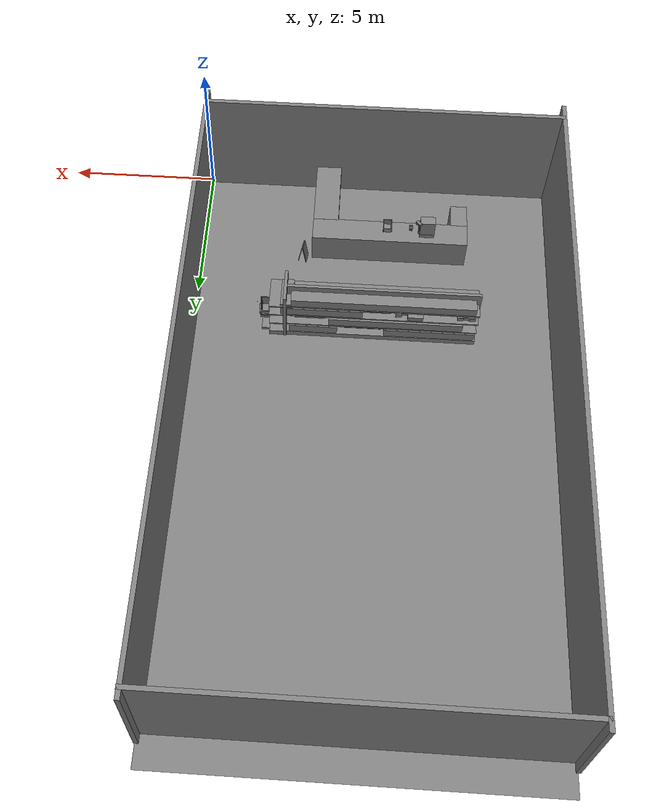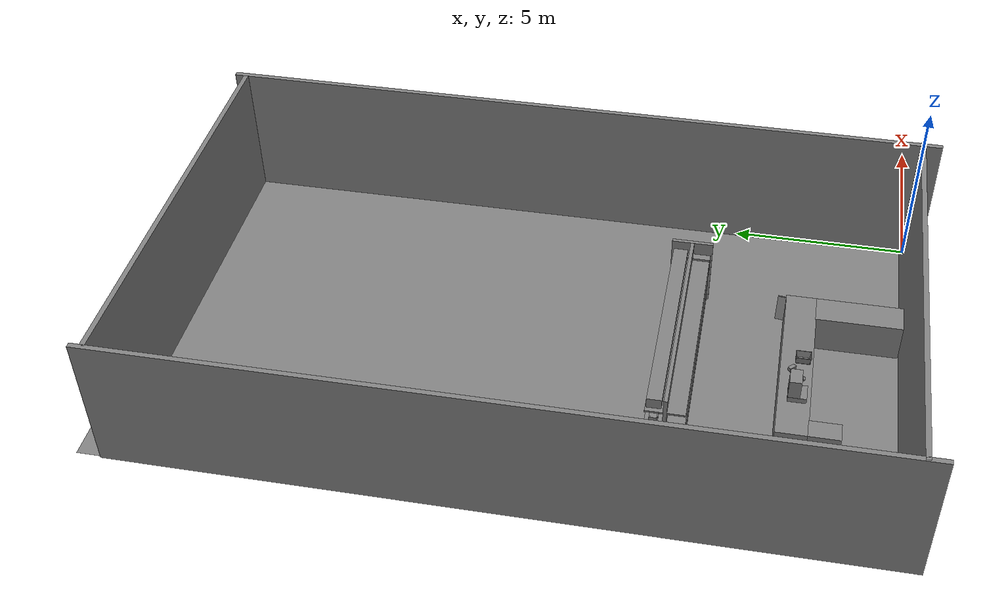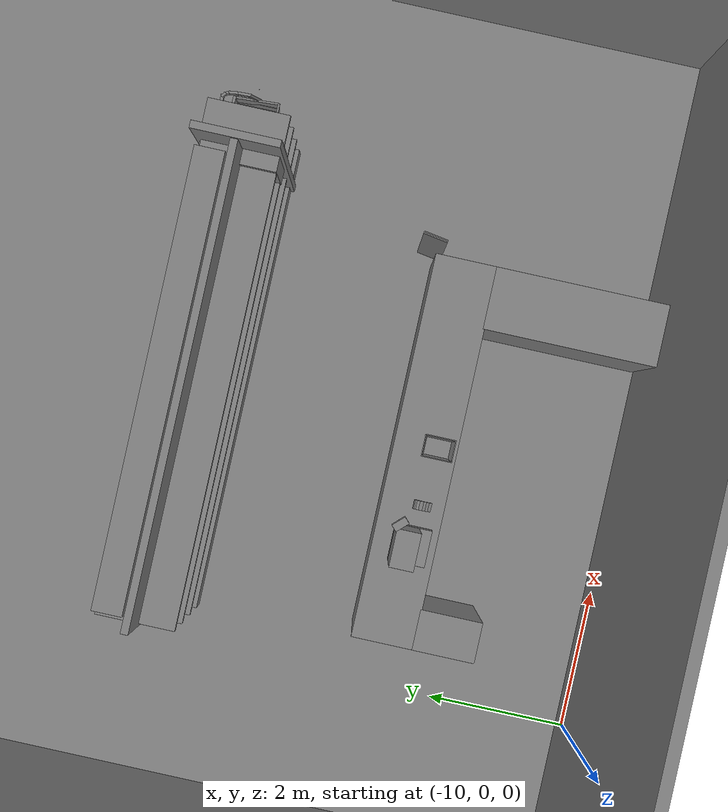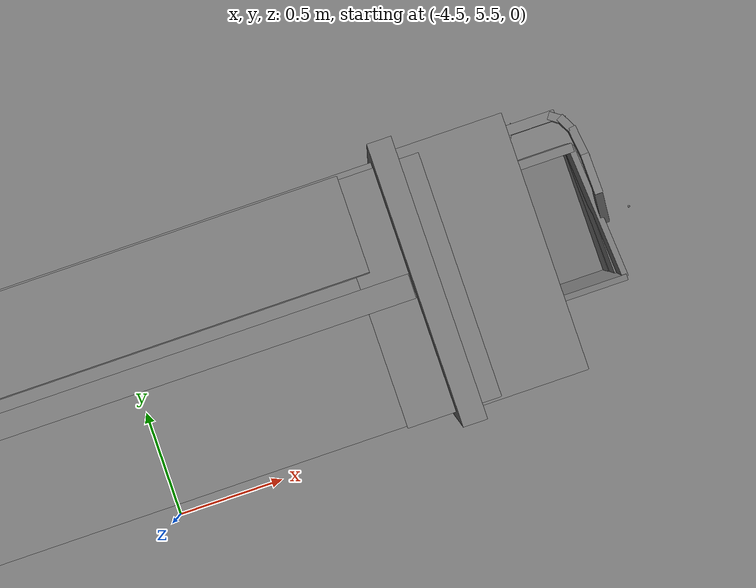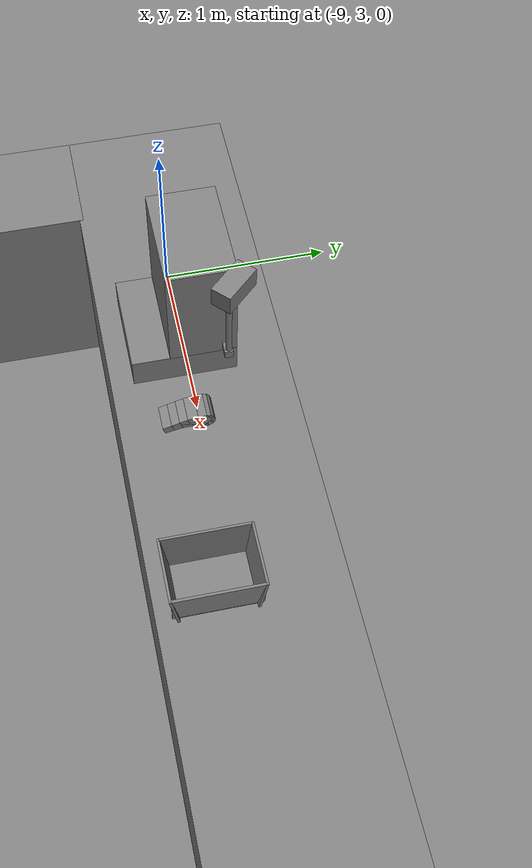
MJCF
<mujoco>
    <option gravity="0.000000000 0.000000000 -9.810000420" timestep="0.0166666" integrator="implicitfast" density="1.225" viscosity="1.8000001e-05" noslip_iterations="10" iterations="100" sdf_iterations="50">
        <flag multiccd="disable"/>
    </option>
    <size memory="1000M"/>
    <compiler coordinate="local"/>
    <worldbody>
        <light cutoff="30" pos="0 1 1" dir="0 -1 -2"/>
        <light cutoff="30" pos="0 -1 1" dir="0 1 -2"/>
        <body pos="-2.436573029 6.404376507 0.137849092" euler="0.000000000 0.000000000 0.000000000" name="openloong_gripper_2f85_fix_base_usda_shoppingtrolley_01">
            <geom contype="1" conaffinity="1" density="1000" type="box" material="" rgba="0.500000000 0.500000000 0.500000000 1.000000000" solimp="0.899999976 0.949999988 0.001000000" friction="1.000000000 0.005000000 0.000100000" solref="0.020000000 1.000000000" margin="0" condim="3" group="0" pos="-0.107458733 0.238907143 0.911498845" quat="0.634576976 0.622505128 -0.330067992 -0.317575932" size="0.017999999 0.022499999 0.035999998" name="openloong_gripper_2f85_fix_base_usda_geom_2B92B4FB_77AE_4224_892A_4FF31F940338"/>
            <geom contype="1" conaffinity="1" density="1000" type="box" material="" rgba="0.500000000 0.500000000 0.500000000 1.000000000" solimp="0.899999976 0.949999988 0.001000000" friction="1.000000000 0.005000000 0.000100000" solref="0.020000000 1.000000000" margin="0" condim="3" group="0" pos="-0.126757339 -0.182533979 0.598989725" quat="0.996607184 0.055331606 -0.059003651 -0.015205891" size="0.013499999 0.287999988 0.053999998" name="openloong_gripper_2f85_fix_base_usda_geom_F5F14F06_9796_41EA_877E_C2D14F87BEE8"/>
            <geom contype="1" conaffinity="1" density="1000" type="box" material="" rgba="0.500000000 0.500000000 0.500000000 1.000000000" solimp="0.899999976 0.949999988 0.001000000" friction="1.000000000 0.005000000 0.000100000" solref="0.020000000 1.000000000" margin="0" condim="3" group="0" pos="-0.005004787 0.248085022 0.912686050" quat="1.000000000 0.000000000 0.000000000 0.000000000" size="0.107999995 0.022499999 0.022499999" name="openloong_gripper_2f85_fix_base_usda_geom_386DBAE2_4AF1_478D_B88B_060475CE389A"/>
            <geom contype="1" conaffinity="1" density="1000" type="box" material="" rgba="0.500000000 0.500000000 0.500000000 1.000000000" solimp="0.899999976 0.949999988 0.001000000" friction="1.000000000 0.005000000 0.000100000" solref="0.020000000 1.000000000" margin="0" condim="3" group="0" pos="-0.169898406 -0.043119621 0.915120542" quat="0.687021017 0.726584017 -0.005590606 -0.006832919" size="0.017999999 0.022499999 0.089999996" name="openloong_gripper_2f85_fix_base_usda_geom_FE5048CD_5A54_480E_B614_607EB0716C25"/>
            <geom contype="1" conaffinity="1" density="1000" type="box" material="" rgba="0.500000000 0.500000000 0.500000000 1.000000000" solimp="0.899999976 0.949999988 0.001000000" friction="1.000000000 0.005000000 0.000100000" solref="0.020000000 1.000000000" margin="0" condim="3" group="0" pos="0.148195267 -0.199506566 0.782808602" quat="0.998808920 0.017156634 0.026950166 0.036880098" size="0.013499999 0.305999994 0.063000001" name="openloong_gripper_2f85_fix_base_usda_geom_2975E602_7E92_4396_A58C_E5707339CA94"/>
            <geom contype="1" conaffinity="1" density="1000" type="box" material="" rgba="0.500000000 0.500000000 0.500000000 1.000000000" solimp="0.899999976 0.949999988 0.001000000" friction="1.000000000 0.005000000 0.000100000" solref="0.020000000 1.000000000" margin="0" condim="3" group="0" pos="-0.142927840 -0.199506134 0.784674108" quat="0.998421252 0.016904408 -0.027109101 -0.046199299" size="0.013499999 0.305999994 0.063000001" name="openloong_gripper_2f85_fix_base_usda_geom_1DBEB680_6157_4EF2_A11F_FC19D4AA0EE5"/>
            <geom contype="1" conaffinity="1" density="1000" type="box" material="" rgba="0.500000000 0.500000000 0.500000000 1.000000000" solimp="0.899999976 0.949999988 0.001000000" friction="1.000000000 0.005000000 0.000100000" solref="0.020000000 1.000000000" margin="0" condim="3" group="0" pos="-0.000004721 -0.174527690 0.560063601" quat="0.996704638 0.081116498 -0.000000004 0.000000000" size="0.126000002 0.287999988 0.009000000" name="openloong_gripper_2f85_fix_base_usda_geom_6DDC1DB3_1EA2_41F5_BD02_56688F73336C"/>
            <geom contype="1" conaffinity="1" density="1000" type="box" material="" rgba="0.500000000 0.500000000 0.500000000 1.000000000" solimp="0.899999976 0.949999988 0.001000000" friction="1.000000000 0.005000000 0.000100000" solref="0.020000000 1.000000000" margin="0" condim="3" group="0" pos="-0.160832763 0.103427693 0.910528183" quat="0.711469591 0.699786782 -0.048386075 -0.042050660" size="0.017999999 0.022499999 0.071999997" name="openloong_gripper_2f85_fix_base_usda_geom_6B0C9F61_2FF2_4601_8B5F_10ADD714217F"/>
            <geom contype="1" conaffinity="1" density="1000" type="box" material="" rgba="0.500000000 0.500000000 0.500000000 1.000000000" solimp="0.899999976 0.949999988 0.001000000" friction="1.000000000 0.005000000 0.000100000" solref="0.020000000 1.000000000" margin="0" condim="3" group="0" pos="-0.169898406 -0.178061336 0.864131629" quat="0.916343808 -0.400392294 -0.000000045 0.000000030" size="0.017999999 0.022499999 0.089999996" name="openloong_gripper_2f85_fix_base_usda_geom_963AEC07_676A_408B_A1B3_F26206C95B65"/>
            <geom contype="1" conaffinity="1" density="1000" type="box" material="" rgba="0.500000000 0.500000000 0.500000000 1.000000000" solimp="0.899999976 0.949999988 0.001000000" friction="1.000000000 0.005000000 0.000100000" solref="0.020000000 1.000000000" margin="0" condim="3" group="0" pos="-0.000006008 -0.484932661 0.670727849" quat="0.997585475 0.069449045 -0.000000004 -0.000000089" size="0.179999992 0.013499999 0.170999989" name="openloong_gripper_2f85_fix_base_usda_geom_54B7ED62_5FEE_4BB5_8FF9_55D5A89E9C40"/>
            <geom contype="1" conaffinity="1" density="1000" type="box" material="" rgba="0.500000000 0.500000000 0.500000000 1.000000000" solimp="0.899999976 0.949999988 0.001000000" friction="1.000000000 0.005000000 0.000100000" solref="0.020000000 1.000000000" margin="0" condim="3" group="0" pos="0.134013891 0.200098798 0.912192523" quat="0.692574680 -0.680924535 -0.166899428 0.169783980" size="0.017999999 0.022499999 0.035999998" name="openloong_gripper_2f85_fix_base_usda_geom_BC4EBABC_2EB8_473E_B8A7_4A4B1BE7903C"/>
            <geom contype="1" conaffinity="1" density="1000" type="box" material="" rgba="0.500000000 0.500000000 0.500000000 1.000000000" solimp="0.899999976 0.949999988 0.001000000" friction="1.000000000 0.005000000 0.000100000" solref="0.020000000 1.000000000" margin="0" condim="3" group="0" pos="0.141839072 -0.191051379 0.702451229" quat="0.997147262 0.056065105 0.045779929 0.021407485" size="0.013499999 0.287999988 0.053999998" name="openloong_gripper_2f85_fix_base_usda_geom_E13365BB_7268_4593_A5AA_684B7E0CD6F6"/>
            <geom contype="1" conaffinity="1" density="1000" type="box" material="" rgba="0.500000000 0.500000000 0.500000000 1.000000000" solimp="0.899999976 0.949999988 0.001000000" friction="1.000000000 0.005000000 0.000100000" solref="0.020000000 1.000000000" margin="0" condim="3" group="0" pos="0.169898629 -0.178061336 0.864131629" quat="0.916343808 -0.400392294 -0.000000045 0.000000030" size="0.017999999 0.022499999 0.089999996" name="openloong_gripper_2f85_fix_base_usda_geom_9AAABF67_4C0F_4B75_872F_DD9CCE4F819A"/>
            <geom contype="1" conaffinity="1" density="1000" type="box" material="" rgba="0.500000000 0.500000000 0.500000000 1.000000000" solimp="0.899999976 0.949999988 0.001000000" friction="1.000000000 0.005000000 0.000100000" solref="0.020000000 1.000000000" margin="0" condim="3" group="0" pos="-0.000005364 0.100332208 0.734785020" quat="0.999668717 0.025737956 -0.000000010 0.000000000" size="0.135000005 0.019800000 0.152999997" name="openloong_gripper_2f85_fix_base_usda_geom_751E5345_EBAB_437F_8527_94D781E5B647"/>
            <geom contype="1" conaffinity="1" density="1000" type="box" material="" rgba="0.500000000 0.500000000 0.500000000 1.000000000" solimp="0.899999976 0.949999988 0.001000000" friction="1.000000000 0.005000000 0.000100000" solref="0.020000000 1.000000000" margin="0" condim="3" group="0" pos="-0.012634277 -0.174527690 -0.088243507" quat="1.000000000 0.000000000 -0.000000004 0.000000000" size="0.135000005 0.287999988 0.044999998" name="openloong_gripper_2f85_fix_base_usda_geom_DDBE5E6C_FA25_4099_A19F_566536303253"/>
            <geom contype="1" conaffinity="1" density="1000" type="box" material="" rgba="0.500000000 0.500000000 0.500000000 1.000000000" solimp="0.899999976 0.949999988 0.001000000" friction="1.000000000 0.005000000 0.000100000" solref="0.020000000 1.000000000" margin="0" condim="3" group="0" pos="0.131482959 -0.182533979 0.598989725" quat="0.996607125 0.055331629 0.059003670 0.015205893" size="0.013499999 0.287999988 0.053999998" name="openloong_gripper_2f85_fix_base_usda_geom_8B49DF05_1C96_40A6_9EE2_72C49CD48CDE"/>
            <geom contype="1" conaffinity="1" density="1000" type="box" material="" rgba="0.500000000 0.500000000 0.500000000 1.000000000" solimp="0.899999976 0.949999988 0.001000000" friction="1.000000000 0.005000000 0.000100000" solref="0.020000000 1.000000000" margin="0" condim="3" group="0" pos="0.103667587 0.233050480 0.912927270" quat="0.634205043 -0.622199059 -0.324503720 0.324576139" size="0.017999999 0.022499999 0.035999998" name="openloong_gripper_2f85_fix_base_usda_geom_484A906A_ACB8_4945_B63D_AF077ED67EBA"/>
            <geom contype="1" conaffinity="1" density="1000" type="box" material="" rgba="0.500000000 0.500000000 0.500000000 1.000000000" solimp="0.899999976 0.949999988 0.001000000" friction="1.000000000 0.005000000 0.000100000" solref="0.020000000 1.000000000" margin="0" condim="3" group="0" pos="-0.134013891 0.200098798 0.912192523" quat="0.694057047 0.679413557 -0.172947660 -0.163618833" size="0.017999999 0.022499999 0.035999998" name="openloong_gripper_2f85_fix_base_usda_geom_2D67766D_7F74_4855_9A81_55EA933B3CAC"/>
            <geom contype="1" conaffinity="1" density="1000" type="box" material="" rgba="0.500000000 0.500000000 0.500000000 1.000000000" solimp="0.899999976 0.949999988 0.001000000" friction="1.000000000 0.005000000 0.000100000" solref="0.020000000 1.000000000" margin="0" condim="3" group="0" pos="-0.135714188 -0.191051379 0.694841146" quat="0.997147322 0.056064609 -0.045779683 -0.021407485" size="0.013499999 0.287999988 0.053999998" name="openloong_gripper_2f85_fix_base_usda_geom_B9794A8F_2B78_4A36_BBA9_34427D29AD80"/>
            <geom contype="1" conaffinity="1" density="1000" type="box" material="" rgba="0.500000000 0.500000000 0.500000000 1.000000000" solimp="0.899999976 0.949999988 0.001000000" friction="1.000000000 0.005000000 0.000100000" solref="0.020000000 1.000000000" margin="0" condim="3" group="0" pos="0.169898629 -0.043119621 0.915120542" quat="0.687029123 -0.726576388 -0.006509603 0.005963952" size="0.017999999 0.022499999 0.089999996" name="openloong_gripper_2f85_fix_base_usda_geom_4351035B_4D15_4819_8278_4EC7D340CBA4"/>
            <geom contype="1" conaffinity="1" density="1000" type="box" material="" rgba="0.500000000 0.500000000 0.500000000 1.000000000" solimp="0.899999976 0.949999988 0.001000000" friction="1.000000000 0.005000000 0.000100000" solref="0.020000000 1.000000000" margin="0" condim="3" group="0" pos="0.160832971 0.103427693 0.910528183" quat="0.711112797 -0.700149298 -0.042821646 0.047705106" size="0.017999999 0.022499999 0.071999997" name="openloong_gripper_2f85_fix_base_usda_geom_3A9997C4_9B6B_49A8_9E6E_0B7334CBDD5F"/>
            <freejoint name="openloong_gripper_2f85_fix_base_usda_shoppingtrolley_01_joint"/>
            <site size="0.005000000 0.005000000 0.005000000" rgba="0.500000000 0.500000000 0.500000000 1.000000000" pos="0.000000000 0.000000000 0.000000000" quat="1.000000000 0.000000000 0.000000000 0.000000000" group="0" type="sphere" name="openloong_gripper_2f85_fix_base_usda_shoppingtrolley_01"/>
        </body>
        <body pos="-7.168000221 2.823999882 1.227496982" euler="-0.283413887 0.056829713 -0.133293241" name="openloong_gripper_2f85_fix_base_usda_Pos">
            <geom contype="1" conaffinity="1" density="1000" type="box" material="" rgba="0.500000000 0.500000000 0.500000000 1.000000000" solimp="0.899999976 0.949999988 0.001000000" friction="1.000000000 0.005000000 0.000100000" solref="0.020000000 1.000000000" margin="0" condim="3" group="0" pos="-0.002278805 0.074524641 -0.004134178" quat="0.315989256 0.948762834 0.000000000 0.000000000" size="0.059999999 0.013000000 0.035000000" name="openloong_gripper_2f85_fix_base_usda_geom_D04E1BF7_8093_42E7_96ED_92168B497188"/>
            <geom contype="1" conaffinity="1" density="1000" type="box" material="" rgba="0.500000000 0.500000000 0.500000000 1.000000000" solimp="0.899999976 0.949999988 0.001000000" friction="1.000000000 0.005000000 0.000100000" solref="0.020000000 1.000000000" margin="0" condim="3" group="0" pos="-0.002278805 0.078031301 0.008128285" quat="0.990447283 -0.137893349 -0.000000000 0.000000000" size="0.059999999 0.010000000 0.035000000" name="openloong_gripper_2f85_fix_base_usda_geom_CA347D4E_E836_4B23_972A_886754FC2EAE"/>
            <geom contype="1" conaffinity="1" density="1000" type="box" material="" rgba="0.500000000 0.500000000 0.500000000 1.000000000" solimp="0.899999976 0.949999988 0.001000000" friction="1.000000000 0.005000000 0.000100000" solref="0.020000000 1.000000000" margin="0" condim="3" group="0" pos="-0.002278805 0.080785275 -0.002596974" quat="0.287325412 -0.957833171 0.000000000 -0.000000000" size="0.059999999 0.013000000 0.035000000" name="openloong_gripper_2f85_fix_base_usda_geom_FEF2A31F_14C5_4F8E_8C8F_4A5F91DF8D4F"/>
            <geom contype="1" conaffinity="1" density="1000" type="box" material="" rgba="0.500000000 0.500000000 0.500000000 1.000000000" solimp="0.899999976 0.949999988 0.001000000" friction="1.000000000 0.005000000 0.000100000" solref="0.020000000 1.000000000" margin="0" condim="3" group="0" pos="-0.002278805 -0.098804474 -0.020147085" quat="0.988851428 0.148906425 0.000000000 -0.000000000" size="0.059999999 0.022000000 0.020000000" name="openloong_gripper_2f85_fix_base_usda_geom_2EC0A3D0_62EE_41DA_91BA_B44A17671DB5"/>
            <geom contype="1" conaffinity="1" density="1000" type="box" material="" rgba="0.500000000 0.500000000 0.500000000 1.000000000" solimp="0.899999976 0.949999988 0.001000000" friction="1.000000000 0.005000000 0.000100000" solref="0.020000000 1.000000000" margin="0" condim="3" group="0" pos="-0.002279282 0.019920349 0.012102842" quat="0.995421529 0.095583312 -0.000000000 0.000000000" size="0.059999999 0.025000000 0.026000001" name="openloong_gripper_2f85_fix_base_usda_geom_2C3A9103_83F0_449A_BE66_535074ED2AD9"/>
            <geom contype="1" conaffinity="1" density="1000" type="box" material="" rgba="0.500000000 0.500000000 0.500000000 1.000000000" solimp="0.899999976 0.949999988 0.001000000" friction="1.000000000 0.005000000 0.000100000" solref="0.020000000 1.000000000" margin="0" condim="3" group="0" pos="-0.002279282 0.005734444 -0.014276981" quat="0.999571502 -0.029275293 -0.000000000 0.000000000" size="0.059999999 0.050000001 0.010000000" name="openloong_gripper_2f85_fix_base_usda_geom_C638AF27_9F9C_40C7_8806_0B993D7D4AFE"/>
            <geom contype="1" conaffinity="1" density="1000" type="box" material="" rgba="0.500000000 0.500000000 0.500000000 1.000000000" solimp="0.899999976 0.949999988 0.001000000" friction="1.000000000 0.005000000 0.000100000" solref="0.020000000 1.000000000" margin="0" condim="3" group="0" pos="-0.002278805 0.079460382 0.007771969" quat="0.922590315 -0.385781497 -0.000000000 0.000000000" size="0.059999999 0.010000000 0.035000000" name="openloong_gripper_2f85_fix_base_usda_geom_DC76C054_126C_43A4_88D2_158D620B36B1"/>
            <geom contype="1" conaffinity="1" density="1000" type="box" material="" rgba="0.500000000 0.500000000 0.500000000 1.000000000" solimp="0.899999976 0.949999988 0.001000000" friction="1.000000000 0.005000000 0.000100000" solref="0.020000000 1.000000000" margin="0" condim="3" group="0" pos="-0.002279282 0.081384182 -0.001320124" quat="0.590483606 -0.807049692 0.000000000 0.000000000" size="0.059999999 0.013000000 0.035000000" name="openloong_gripper_2f85_fix_base_usda_geom_7C8157AC_A6BD_448B_A308_972A5A7B06A6"/>
            <geom contype="1" conaffinity="1" density="1000" type="box" material="" rgba="0.500000000 0.500000000 0.500000000 1.000000000" solimp="0.899999976 0.949999988 0.001000000" friction="1.000000000 0.005000000 0.000100000" solref="0.020000000 1.000000000" margin="0" condim="3" group="0" pos="-0.002278805 -0.059297562 -0.007972836" quat="0.988851428 0.148906425 0.000000000 -0.000000000" size="0.059999999 0.020000000 0.022000000" name="openloong_gripper_2f85_fix_base_usda_geom_4B00ABCD_6772_46EC_8397_5F0326C85E01"/>
            <geom contype="1" conaffinity="1" density="1000" type="box" material="" rgba="0.500000000 0.500000000 0.500000000 1.000000000" solimp="0.899999976 0.949999988 0.001000000" friction="1.000000000 0.005000000 0.000100000" solref="0.020000000 1.000000000" margin="0" condim="3" group="0" pos="-0.002278805 0.076618671 -0.004656911" quat="0.004634960 0.999989390 -0.000000000 0.000000000" size="0.059999999 0.013000000 0.035000000" name="openloong_gripper_2f85_fix_base_usda_geom_99F09DD9_1A6B_4957_B501_17359D333836"/>
            <geom contype="1" conaffinity="1" density="1000" type="box" material="" rgba="0.500000000 0.500000000 0.500000000 1.000000000" solimp="0.899999976 0.949999988 0.001000000" friction="1.000000000 0.005000000 0.000100000" solref="0.020000000 1.000000000" margin="0" condim="3" group="0" pos="-0.002279282 -0.021952629 0.002959967" quat="0.991270185 0.131847635 0.000000000 -0.000000000" size="0.059999999 0.020000000 0.024000000" name="openloong_gripper_2f85_fix_base_usda_geom_D230AAB4_6A25_4D91_93AD_8894CABF2309"/>
            <geom contype="1" conaffinity="1" density="1000" type="box" material="" rgba="0.500000000 0.500000000 0.500000000 1.000000000" solimp="0.899999976 0.949999988 0.001000000" friction="1.000000000 0.005000000 0.000100000" solref="0.020000000 1.000000000" margin="0" condim="3" group="0" pos="-0.002278805 0.081418991 0.002587795" quat="0.803492188 -0.595315576 0.000000000 0.000000000" size="0.059999999 0.013000000 0.035000000" name="openloong_gripper_2f85_fix_base_usda_geom_8007C903_2A4F_4434_88F8_B8083C0AD6FB"/>
            <geom contype="1" conaffinity="1" density="1000" type="box" material="" rgba="0.500000000 0.500000000 0.500000000 1.000000000" solimp="0.899999976 0.949999988 0.001000000" friction="1.000000000 0.005000000 0.000100000" solref="0.020000000 1.000000000" margin="0" condim="3" group="0" pos="-0.002278805 0.061115503 0.008545756" quat="0.999325931 0.036714435 -0.000000000 -0.000000000" size="0.059999999 0.020000000 0.035000000" name="openloong_gripper_2f85_fix_base_usda_geom_922E81FC_60E5_4713_A4B2_D6C6C3FAF0C7"/>
            <freejoint name="openloong_gripper_2f85_fix_base_usda_pos_scan"/>
        </body>
        <body pos="-3.510578632 3.403555870 -0.000000100" euler="0.000000000 0.000000000 40.200675964" name="openloong_gripper_2f85_fix_base_usda_PZ">
            <geom contype="1" conaffinity="1" density="1000" type="box" material="" rgba="0.500000000 0.500000000 0.500000000 1.000000000" solimp="0.899999976 0.949999988 0.001000000" friction="1.000000000 0.005000000 0.000100000" solref="0.020000000 1.000000000" margin="0" condim="3" group="0" pos="-0.047453165 0.056484699 0.373715430" quat="0.934750080 0.077914521 0.028795123 0.345459938" size="0.180000007 0.010000000 0.379999995" name="openloong_gripper_2f85_fix_base_usda_geom_F5CC485D_3065_4FD7_AD83_EE3F8DA51A69"/>
            <geom contype="1" conaffinity="1" density="1000" type="box" material="" rgba="0.500000000 0.500000000 0.500000000 1.000000000" solimp="0.899999976 0.949999988 0.001000000" friction="1.000000000 0.005000000 0.000100000" solref="0.020000000 1.000000000" margin="0" condim="3" group="0" pos="0.047452450 -0.054376602 0.374072611" quat="0.934387863 -0.082143910 -0.030358355 0.345326364" size="0.180000007 0.010000000 0.379999995" name="openloong_gripper_2f85_fix_base_usda_geom_F7B20784_D5F1_48B5_A6B8_BD10495DDA22"/>
            <freejoint name="openloong_gripper_2f85_fix_base_usda_PZ"/>
        </body>
        <body pos="-6.332345009 2.779978037 1.034067392" euler="0.000000000 0.000000000 0.000000000" name="openloong_gripper_2f85_fix_base_usda_basket">
            <geom contype="1" conaffinity="1" density="100000" type="box" material="" rgba="0.500000000 0.500000000 0.500000000 1.000000000" solimp="0.899999976 0.949999988 0.001000000" friction="1.000000000 0.899999976 0.000100000" solref="0.020000000 1.000000000" margin="0" condim="3" group="0" pos="-0.039724827 -0.188568115 0.167089701" quat="0.997537494 0.070135131 0.000000000 0.000000000" size="0.150000006 0.006000000 0.108000003" name="openloong_gripper_2f85_fix_base_usda_geom_7552BC76_DF9E_46CF_96EA_BEAFD739DD00"/>
            <geom contype="1" conaffinity="1" density="100000" type="box" material="" rgba="0.500000000 0.500000000 0.500000000 1.000000000" solimp="0.899999976 0.949999988 0.001000000" friction="1.000000000 0.899999976 0.000100000" solref="0.020000000 1.000000000" margin="0" condim="3" group="0" pos="0.094372749 0.000000000 0.168361664" quat="0.706172049 0.036353335 0.036353379 0.706171215" size="0.200000003 0.006000000 0.108000003" name="openloong_gripper_2f85_fix_base_usda_geom_79CC3922_C63E_4349_BEDB_3339477122C4"/>
            <geom contype="1" conaffinity="1" density="100000" type="box" material="" rgba="0.500000000 0.500000000 0.500000000 1.000000000" solimp="0.899999976 0.949999988 0.001000000" friction="1.000000000 0.899999976 0.000100000" solref="0.020000000 1.000000000" margin="0" condim="3" group="0" pos="-0.039724827 0.000000000 0.068126202" quat="1.000000000 0.000000000 0.000000000 0.000000000" size="0.129999995 0.174999997 0.006000000" name="openloong_gripper_2f85_fix_base_usda_geom_7F02D797_2B29_46B7_9D1D_3109B86F0C4F"/>
            <geom contype="1" conaffinity="1" density="100000" type="box" material="" rgba="0.500000000 0.500000000 0.500000000 1.000000000" solimp="0.899999976 0.949999988 0.001000000" friction="1.000000000 0.899999976 0.000100000" solref="0.020000000 1.000000000" margin="0" condim="3" group="0" pos="-0.039724827 0.188377380 0.167089701" quat="0.997489929 -0.070808925 0.000000000 0.000000000" size="0.150000006 0.006000000 0.108000003" name="openloong_gripper_2f85_fix_base_usda_geom_3AD71C5F_9F23_42EB_AC48_A9D0A692B79A"/>
            <geom contype="1" conaffinity="1" density="100000" type="box" material="" rgba="0.500000000 0.500000000 0.500000000 1.000000000" solimp="0.899999976 0.949999988 0.001000000" friction="1.000000000 0.899999976 0.000100000" solref="0.020000000 1.000000000" margin="0" condim="3" group="0" pos="-0.172339439 0.000000000 0.168361664" quat="0.706172407 -0.036353018 -0.036353093 0.706170976" size="0.200000003 0.006000000 0.108000003" name="openloong_gripper_2f85_fix_base_usda_geom_BFE8263B_0A65_4BDA_B9FE_B41AB9D9A44F"/>
            <freejoint name="openloong_gripper_2f85_fix_base_usda_basket_joint"/>
            <site size="0.005000000 0.005000000 0.005000000" rgba="0.500000000 0.500000000 0.500000000 1.000000000" pos="0.000000000 0.000000000 0.000000000" quat="1.000000000 0.000000000 0.000000000 0.000000000" group="0" type="sphere" name="openloong_gripper_2f85_fix_base_usda_basketsite"/>
        </body>
        <body pos="0.000000000 0.000000000 0.000000000" euler="0.000000000 0.000000000 0.000000000" name=" Static Objects_ Static Objects">
            <geom contype="1" conaffinity="1" density="1000" type="box" material="" rgba="0.500000000 0.500000000 0.500000000 1.000000000" solimp="0.899999976 0.949999988 0.001000000" friction="1.000000000 0.005000000 0.000100000" solref="0.020000000 1.000000000" margin="0" condim="3" group="0" pos="-6.286010742 6.153595448 1.563861728" quat="0.707107067 0.000000000 0.000000000 0.707106471" size="0.529999971 3.134999990 0.025000000" name=" Static Objects_geom_09A32A6B_908F_4725_AF83_A65D25F3F3A1"/>
            <geom contype="1" conaffinity="1" density="1000" type="box" material="" rgba="0.500000000 0.500000000 0.500000000 1.000000000" solimp="0.899999976 0.949999988 0.001000000" friction="1.000000000 0.005000000 0.000100000" solref="0.020000000 1.000000000" margin="0" condim="3" group="0" pos="-3.101639986 6.150595188 1.018643856" quat="1.000000000 0.000000000 0.000000000 0.000000000" size="0.050000001 0.579999983 1.019999981" name=" Static Objects_geom_663DE55D_5317_4459_9CFC_0552E243BEC2"/>
            <geom contype="1" conaffinity="1" density="1000" type="box" material="" rgba="0.500000000 0.500000000 0.500000000 1.000000000" solimp="0.899999976 0.949999988 0.001000000" friction="1.000000000 0.005000000 0.000100000" solref="0.020000000 1.000000000" margin="0" condim="3" group="0" pos="-2.825197220 6.153595448 1.563861728" quat="0.707107067 0.000000000 0.000000000 0.707106471" size="0.550000012 0.239999995 0.025000000" name=" Static Objects_geom_DB84DA27_8C32_44E2_90E2_0E0A66D9F603"/>
            <geom contype="1" conaffinity="1" density="1000" type="box" material="" rgba="0.500000000 0.500000000 0.500000000 1.000000000" solimp="0.899999976 0.949999988 0.001000000" friction="1.000000000 0.005000000 0.000100000" solref="0.020000000 1.000000000" margin="0" condim="3" group="0" pos="-6.311686516 6.153595448 1.018643856" quat="0.707107067 0.000000000 0.000000000 0.707106471" size="0.050000001 3.150000095 1.019999981" name=" Static Objects_geom_6C18585E_ED6F_4F74_ABF9_E0792700F597"/>
            <geom contype="1" conaffinity="1" density="1000" type="box" material="" rgba="0.500000000 0.500000000 0.500000000 1.000000000" solimp="0.899999976 0.949999988 0.001000000" friction="1.000000000 0.005000000 0.000100000" solref="0.020000000 1.000000000" margin="0" condim="3" group="0" pos="-2.825197220 6.153595448 1.115278244" quat="0.707107067 0.000000000 0.000000000 0.707106471" size="0.550000012 0.239999995 0.025000000" name=" Static Objects_geom_D7525B32_2EE3_4A7A_B0E1_E682A332E980"/>
            <geom contype="1" conaffinity="1" density="1000" type="box" material="" rgba="0.500000000 0.500000000 0.500000000 1.000000000" solimp="0.899999976 0.949999988 0.001000000" friction="1.000000000 0.005000000 0.000100000" solref="0.020000000 1.000000000" margin="0" condim="3" group="0" pos="-6.293097973 6.153595448 1.114443064" quat="0.707107067 0.000000000 0.000000000 0.707106471" size="0.529999971 3.134999990 0.025000000" name=" Static Objects_geom_09D63FC1_39FB_45E6_84E7_D6A33841F88A"/>
            <geom contype="1" conaffinity="1" density="1000" type="box" material="" rgba="0.500000000 0.500000000 0.500000000 1.000000000" solimp="0.899999976 0.949999988 0.001000000" friction="1.000000000 0.005000000 0.000100000" solref="0.020000000 1.000000000" margin="0" condim="3" group="0" pos="-2.825197220 6.153595448 0.629031777" quat="0.707107067 0.000000000 0.000000000 0.707106471" size="0.550000012 0.239999995 0.025000000" name=" Static Objects_geom_721C6DB2_C469_4CB9_A9A3_AA66F593DE58"/>
            <geom contype="1" conaffinity="1" density="1000" type="box" material="" rgba="0.500000000 0.500000000 0.500000000 1.000000000" solimp="0.899999976 0.949999988 0.001000000" friction="1.000000000 0.005000000 0.000100000" solref="0.020000000 1.000000000" margin="0" condim="3" group="0" pos="-6.286010742 6.153595448 0.096129179" quat="0.707107067 0.000000000 0.000000000 0.707106471" size="0.529999971 3.134999990 0.098999999" name=" Static Objects_geom_8292E39A_9FCF_475C_89CC_11834F48B963"/>
            <geom contype="1" conaffinity="1" density="1000" type="box" material="" rgba="0.500000000 0.500000000 0.500000000 1.000000000" solimp="0.899999976 0.949999988 0.001000000" friction="1.000000000 0.005000000 0.000100000" solref="0.020000000 1.000000000" margin="0" condim="3" group="0" pos="-2.825197220 6.153595448 0.097434282" quat="0.707107067 0.000000000 0.000000000 0.707106471" size="0.550000012 0.239999995 0.098999999" name=" Static Objects_geom_6EF3DE7F_2AB5_45C3_87CD_C793FFC690FB"/>
            <geom contype="1" conaffinity="1" density="1000" type="box" material="" rgba="0.500000000 0.500000000 0.500000000 1.000000000" solimp="0.899999976 0.949999988 0.001000000" friction="1.000000000 0.005000000 0.000100000" solref="0.020000000 1.000000000" margin="0" condim="3" group="0" pos="-6.286010742 6.153595448 0.629031777" quat="0.707107067 0.000000000 0.000000000 0.707106471" size="0.529999971 3.134999990 0.025000000" name=" Static Objects_geom_BE6F901A_7547_45E5_988B_748DEA3ACD48"/>
            <geom contype="1" conaffinity="1" density="1000" type="box" material="" rgba="0.500000000 0.500000000 0.500000000 1.000000000" solimp="0.899999976 0.949999988 0.001000000" friction="1.000000000 0.005000000 0.000100000" solref="0.020000000 1.000000000" margin="0" condim="3" group="0" pos="-6.000000000 20.159999847 2.000000000" quat="1.000000000 0.000000000 0.000000000 0.000000000" size="6.079999924 0.070000000 2.000000000" name=" Static Objects_geom_A0C86EB2_E7A9_44AD_B260_0B1EB695F0C6"/>
            <geom contype="1" conaffinity="1" density="1000" type="box" material="" rgba="0.500000000 0.500000000 0.500000000 1.000000000" solimp="0.899999976 0.949999988 0.001000000" friction="1.000000000 0.005000000 0.000100000" solref="0.020000000 1.000000000" margin="0" condim="3" group="0" pos="-6.000000000 0.035000000 2.000000000" quat="1.000000000 0.000000000 0.000000000 0.000000000" size="6.079999924 0.070000000 2.000000000" name=" Static Objects_geom_DFAA0D83_328B_46DD_AC74_4E1CD1FF46E4"/>
            <geom contype="1" conaffinity="1" density="1000" type="box" material="" rgba="0.500000000 0.500000000 0.500000000 1.000000000" solimp="0.899999976 0.949999988 0.001000000" friction="1.000000000 0.005000000 0.000100000" solref="0.020000000 1.000000000" margin="0" condim="3" group="0" pos="0.000000000 10.000000000 2.000000000" quat="1.000000000 0.000000000 0.000000000 0.000000000" size="0.070000000 10.500000000 2.000000000" name=" Static Objects_geom_4E3DC3DF_590D_404A_90E4_62E8BF59657D"/>
            <geom contype="1" conaffinity="1" density="1000" type="box" material="" rgba="0.500000000 0.500000000 0.500000000 1.000000000" solimp="0.899999976 0.949999988 0.001000000" friction="1.000000000 0.005000000 0.000100000" solref="0.020000000 1.000000000" margin="0" condim="3" group="0" pos="-12.050000191 10.000000000 2.000000000" quat="1.000000000 0.000000000 0.000000000 0.000000000" size="0.070000000 10.500000000 2.000000000" name=" Static Objects_geom_CC0C2DF4_46FB_4D09_B744_AD982458A5F3"/>
            <geom contype="1" conaffinity="1" density="1000" type="plane" material="" rgba="0.500000000 0.500000000 0.500000000 1.000000000" solimp="0.899999976 0.949999988 0.001000000" friction="1.000000000 0.005000000 0.000100000" solref="0.020000000 1.000000000" margin="0" condim="3" group="0" pos="-6.000000000 10.399999619 0.000000000" quat="1.000000000 0.000000000 0.000000000 0.000000000" size="6.050000191 10.800000191 0.010000000" name=" Static Objects_geom_2DF12337_79B2_470A_9706_5C8620FA9C25"/>
            <geom contype="1" conaffinity="1" density="1000" type="box" material="" rgba="0.500000000 0.500000000 0.500000000 1.000000000" solimp="0.899999976 0.949999988 0.001000000" friction="1.000000000 0.005000000 0.000100000" solref="0.020000000 1.000000000" margin="0" condim="3" group="0" pos="-8.830721855 2.096410990 0.549305558" quat="1.000000000 0.000000000 0.000000000 0.000000000" size="0.280000001 0.430000007 0.550000012" name=" Static Objects_geom_4D07437F_1284_4F97_8F01_87C966C8CCA6"/>
            <geom contype="1" conaffinity="1" density="1000" type="box" material="" rgba="0.500000000 0.500000000 0.500000000 1.000000000" solimp="0.899999976 0.949999988 0.001000000" friction="1.000000000 0.005000000 0.000100000" solref="0.020000000 1.000000000" margin="0" condim="3" group="0" pos="-6.460197449 2.937205315 0.548931718" quat="1.000000000 0.000000000 0.000000000 0.000000000" size="2.650000095 0.430000007 0.550000012" name=" Static Objects_geom_C2DDB941_E664_4C16_8F0C_AD88E3C2FDED"/>
            <geom contype="1" conaffinity="1" density="1000" type="box" material="" rgba="0.500000000 0.500000000 0.500000000 1.000000000" solimp="0.899999976 0.949999988 0.001000000" friction="1.000000000 0.005000000 0.000100000" solref="0.020000000 1.000000000" margin="0" condim="3" group="0" pos="-4.240264893 1.327049494 0.549888909" quat="1.000000000 0.000000000 0.000000000 0.000000000" size="0.430000007 1.200000048 0.550000012" name=" Static Objects_geom_1F9229CF_45E1_4384_9FDE_F801B3C2B236"/>
            <geom contype="1" conaffinity="1" density="1000" type="box" material="" rgba="0.500000000 0.500000000 0.500000000 1.000000000" solimp="0.899999976 0.949999988 0.001000000" friction="1.000000000 0.005000000 0.000100000" solref="0.020000000 1.000000000" margin="0" condim="3" group="0" pos="-7.408766270 3.088089943 1.776644945" quat="0.928051054 0.000000000 0.000000000 0.372453064" size="0.050000001 0.100000001 0.050000001" name=" Static Objects_geom_2FC3D5C9_ADE5_4584_8B86_4AB593B48DFF"/>
            <geom contype="1" conaffinity="1" density="1000" type="box" material="" rgba="0.500000000 0.500000000 0.500000000 1.000000000" solimp="0.899999976 0.949999988 0.001000000" friction="1.000000000 0.005000000 0.000100000" solref="0.020000000 1.000000000" margin="0" condim="3" group="0" pos="-7.437745571 3.067511320 1.289965630" quat="1.000000000 0.000000000 0.000000000 0.000000000" size="0.029999999 0.020000000 0.020000000" name=" Static Objects_geom_57F617B8_1877_4144_AC05_2F7FB6861943"/>
            <geom contype="1" conaffinity="1" density="1000" type="box" material="" rgba="0.500000000 0.500000000 0.500000000 1.000000000" solimp="0.899999976 0.949999988 0.001000000" friction="1.000000000 0.005000000 0.000100000" solref="0.020000000 1.000000000" margin="0" condim="3" group="0" pos="-7.719123363 2.867671013 1.173410416" quat="1.000000000 0.000000000 0.000000000 0.000000000" size="0.250000000 0.250000000 0.079999998" name=" Static Objects_geom_0B387630_4932_4E35_8096_66E9B45EAE42"/>
            <geom contype="1" conaffinity="1" density="1000" type="box" material="" rgba="0.500000000 0.500000000 0.500000000 1.000000000" solimp="0.899999976 0.949999988 0.001000000" friction="1.000000000 0.005000000 0.000100000" solref="0.020000000 1.000000000" margin="0" condim="3" group="0" pos="-7.719123363 2.958004713 1.530241251" quat="1.000000000 0.000000000 0.000000000 0.000000000" size="0.250000000 0.159999996 0.280000001" name=" Static Objects_geom_CEBFD364_EBD1_47CB_BD8F_D0679C3DA4AB"/>
            <geom contype="1" conaffinity="1" density="1000" type="cylinder" material="" rgba="0.500000000 0.500000000 0.500000000 1.000000000" solimp="0.899999976 0.949999988 0.001000000" friction="1.000000000 0.005000000 0.000100000" solref="0.020000000 1.000000000" margin="0" condim="3" group="0" pos="-7.427312374 3.069516420 1.502544641" quat="0.928051054 0.000000000 0.000000000 0.372453064" size="0.015000000 0.230000004 0.100000001" name=" Static Objects_geom_371C77EE_96F0_4927_974A_34A99837BEDC"/>
            <geom contype="1" conaffinity="1" density="1000" type="box" material="" rgba="0.500000000 0.500000000 0.500000000 1.000000000" solimp="0.899999976 0.949999988 0.001000000" friction="1.000000000 0.005000000 0.000100000" solref="0.020000000 1.000000000" margin="0" condim="3" group="0" pos="-9.058088303 6.434794426 1.209077358" quat="1.000000000 0.000000000 0.000000000 0.000000000" size="0.250000000 0.100000001 0.070000000" name=" Static Objects_geom_8C4F5F93_28D1_4380_9D2F_60D8D616D147"/>
            <geom contype="1" conaffinity="1" density="1000" type="box" material="" rgba="0.500000000 0.500000000 0.500000000 1.000000000" solimp="0.899999976 0.949999988 0.001000000" friction="1.000000000 0.005000000 0.000100000" solref="0.020000000 1.000000000" margin="0" condim="3" group="0" pos="-5.611940861 6.318420410 0.350975692" quat="1.000000000 0.000000000 0.000000000 0.000000000" size="0.699999988 0.100000001 0.150000006" name=" Static Objects_geom_1A617E2B_F239_4CEC_B683_26C5FB29B6E0"/>
            <geom contype="1" conaffinity="1" density="1000" type="box" material="" rgba="0.500000000 0.500000000 0.500000000 1.000000000" solimp="0.899999976 0.949999988 0.001000000" friction="1.000000000 0.005000000 0.000100000" solref="0.020000000 1.000000000" margin="0" condim="3" group="0" pos="-9.237723351 6.464855671 1.209077358" quat="1.000000000 0.000000000 0.000000000 0.000000000" size="0.100000001 0.100000001 0.070000000" name=" Static Objects_geom_F3076834_145D_4D47_9DC8_5EAA08A1D9D7"/>
            <geom contype="1" conaffinity="1" density="1000" type="box" material="" rgba="0.500000000 0.500000000 0.500000000 1.000000000" solimp="0.899999976 0.949999988 0.001000000" friction="1.000000000 0.005000000 0.000100000" solref="0.020000000 1.000000000" margin="0" condim="3" group="0" pos="-6.300771236 6.459744930 1.744376063" quat="1.000000000 0.000000000 0.000000000 0.000000000" size="3.000000000 0.200000003 0.150000006" name=" Static Objects_geom_73BF280D_90CB_4DA7_A1CA_51147F7A719B"/>
            <geom contype="1" conaffinity="1" density="1000" type="box" material="" rgba="0.500000000 0.500000000 0.500000000 1.000000000" solimp="0.899999976 0.949999988 0.001000000" friction="1.000000000 0.005000000 0.000100000" solref="0.020000000 1.000000000" margin="0" condim="3" group="0" pos="-7.373087406 6.458900928 1.214329123" quat="1.000000000 0.000000000 0.000000000 0.000000000" size="0.250000000 0.200000003 0.075000003" name=" Static Objects_geom_62D52563_D871_47E0_9FC5_8C9086FBA05C"/>
            <geom contype="1" conaffinity="1" density="1000" type="box" material="" rgba="0.500000000 0.500000000 0.500000000 1.000000000" solimp="0.899999976 0.949999988 0.001000000" friction="1.000000000 0.005000000 0.000100000" solref="0.020000000 1.000000000" margin="0" condim="3" group="0" pos="-4.035642624 6.459744930 0.352518857" quat="1.000000000 0.000000000 0.000000000 0.000000000" size="0.800000012 0.200000003 0.150000006" name=" Static Objects_geom_A526B585_FD21_47F3_9807_3C29C29FF053"/>
            <geom contype="1" conaffinity="1" density="1000" type="box" material="" rgba="0.500000000 0.500000000 0.500000000 1.000000000" solimp="0.899999976 0.949999988 0.001000000" friction="1.000000000 0.005000000 0.000100000" solref="0.020000000 1.000000000" margin="0" condim="3" group="0" pos="-3.907610416 6.318625927 0.800981164" quat="1.000000000 0.000000000 0.000000000 0.000000000" size="0.500000000 0.100000001 0.150000006" name=" Static Objects_geom_7ABD59F3_FF9F_4330_94A6_F5AE978E911A"/>
            <geom contype="1" conaffinity="1" density="1000" type="box" material="" rgba="0.500000000 0.500000000 0.500000000 1.000000000" solimp="0.899999976 0.949999988 0.001000000" friction="1.000000000 0.005000000 0.000100000" solref="0.020000000 1.000000000" margin="0" condim="3" group="0" pos="-6.098561764 6.327973843 1.292199373" quat="1.000000000 0.000000000 0.000000000 0.000000000" size="0.500000000 0.100000001 0.150000006" name=" Static Objects_geom_2ED25936_4069_4ED9_8184_2A556190EE3C"/>
            <geom contype="1" conaffinity="1" density="1000" type="box" material="" rgba="0.500000000 0.500000000 0.500000000 1.000000000" solimp="0.899999976 0.949999988 0.001000000" friction="1.000000000 0.005000000 0.000100000" solref="0.020000000 1.000000000" margin="0" condim="3" group="0" pos="-7.886891365 6.459744930 0.352518857" quat="1.000000000 0.000000000 0.000000000 0.000000000" size="1.500000000 0.200000003 0.150000006" name=" Static Objects_geom_07AF0BF6_E780_44EB_90A4_ADCD03610C11"/>
            <geom contype="1" conaffinity="1" density="1000" type="box" material="" rgba="0.500000000 0.500000000 0.500000000 1.000000000" solimp="0.899999976 0.949999988 0.001000000" friction="1.000000000 0.005000000 0.000100000" solref="0.020000000 1.000000000" margin="0" condim="3" group="0" pos="-6.824534416 6.447464466 1.212718010" quat="1.000000000 0.000000000 0.000000000 0.000000000" size="0.100000001 0.100000001 0.075000003" name=" Static Objects_geom_39143219_66B2_4F17_9DD2_896AD6B455AC"/>
            <geom contype="1" conaffinity="1" density="1000" type="box" material="" rgba="0.500000000 0.500000000 0.500000000 1.000000000" solimp="0.899999976 0.949999988 0.001000000" friction="1.000000000 0.005000000 0.000100000" solref="0.020000000 1.000000000" margin="0" condim="3" group="0" pos="-4.407354832 6.459744930 1.292199373" quat="1.000000000 0.000000000 0.000000000 0.000000000" size="1.240000010 0.200000003 0.150000006" name=" Static Objects_geom_39C9E8AC_FDE1_4143_9709_3A4DA53E9232"/>
            <geom contype="1" conaffinity="1" density="1000" type="box" material="" rgba="0.500000000 0.500000000 0.500000000 1.000000000" solimp="0.899999976 0.949999988 0.001000000" friction="1.000000000 0.005000000 0.000100000" solref="0.020000000 1.000000000" margin="0" condim="3" group="0" pos="-6.751636982 6.459744930 0.800981164" quat="1.000000000 0.000000000 0.000000000 0.000000000" size="2.200000048 0.200000003 0.150000006" name=" Static Objects_geom_0AE02EE7_3358_434D_8002_176FE7AD7F72"/>
            <geom contype="1" conaffinity="1" density="1000" type="box" material="" rgba="0.500000000 0.500000000 0.500000000 1.000000000" solimp="0.899999976 0.949999988 0.001000000" friction="1.000000000 0.005000000 0.000100000" solref="0.020000000 1.000000000" margin="0" condim="3" group="0" pos="-6.924745083 6.362090111 1.214329123" quat="1.000000000 0.000000000 0.000000000 0.000000000" size="0.200000003 0.100000001 0.075000003" name=" Static Objects_geom_10450577_205E_45D0_8C47_64900368819F"/>
            <geom contype="1" conaffinity="1" density="1000" type="box" material="" rgba="0.500000000 0.500000000 0.500000000 1.000000000" solimp="0.899999976 0.949999988 0.001000000" friction="1.000000000 0.005000000 0.000100000" solref="0.020000000 1.000000000" margin="0" condim="3" group="0" pos="-8.844120979 6.464855671 1.209077358" quat="1.000000000 0.000000000 0.000000000 0.000000000" size="0.100000001 0.100000001 0.070000000" name=" Static Objects_geom_6BC5C2BB_1E6C_49F7_9AE9_597DD0E5C962"/>
            <geom contype="1" conaffinity="1" density="1000" type="box" material="" rgba="0.500000000 0.500000000 0.500000000 1.000000000" solimp="0.899999976 0.949999988 0.001000000" friction="1.000000000 0.005000000 0.000100000" solref="0.020000000 1.000000000" margin="0" condim="3" group="0" pos="-3.157672644 6.136868477 1.348373055" quat="1.000000000 0.000000000 0.000000000 0.000000000" size="0.200000003 0.519999981 0.300000012" name=" Static Objects_geom_10CCEFB5_C283_48C7_941E_A67DA15CC7B5"/>
        </body>
        <body pos="0.000000000 0.000000000 0.000000000" euler="0.000000000 0.000000000 0.000000000" name="Interactive Objects_Interactive Objects"/>
        <body pos="-2.162922621 6.180304527 -0.123990871" euler="0.000000000 0.000000000 180.000000000" mocap="true" name="openloong_gripper_2f85_fix_base_usda_leftHandMocap"/>
        <body pos="-2.162922621 6.180304527 -0.123990871" euler="0.000000000 0.000000000 180.000000000" mocap="true" name="openloong_gripper_2f85_fix_base_usda_rightHandMocap"/>
        <body pos="-2.162922621 6.180304527 1.076009154" euler="0.000000000 0.000000000 180.000000000" name="openloong_gripper_2f85_fix_base_usda_base_link">
            <geom contype="1" conaffinity="1" density="1000" type="mesh" material="" rgba="0.783999979 0.783999979 0.783999979 1.000000000" solimp="0.899999976 0.949999988 0.001000000" friction="1.000000000 0.005000000 0.000100000" solref="0.020000000 1.000000000" margin="0" condim="3" group="3" mesh="base_link" pos="0.000000000 0.000000000 0.000000000" quat="1.000000000 0.000000000 0.000000000 0.000000000" size="1.000000000 1.000000000 1.000000000" name="openloong_gripper_2f85_fix_base_usda__geom_7_A3D9C1DE_A2D3_4B91_AF02_714268A36D4A"/>
            <site size="0.005000000 0.005000000 0.005000000" rgba="0.500000000 0.500000000 0.500000000 1.000000000" pos="0.000000000 0.000000000 0.000000000" quat="1.000000000 0.000000000 0.000000000 0.000000000" group="0" type="sphere" name="openloong_gripper_2f85_fix_base_usda_imu"/>
            <inertial mass="22.447001" pos="-0.005664100 -0.001336700 0.238289997" diaginertia="0.374352545 0.277180195 0.220617250" quat="0.999247074 0.035235517 -0.015086859 0.006023135"/>
            <body pos="0.000000000 0.000000000 0.300000072" euler="0.000000000 0.000000000 0.000000000" name="openloong_gripper_2f85_fix_base_usda_dummy_body">
                <geom contype="1" conaffinity="1" density="1000" type="sphere" material="" rgba="0.783999979 0.783999979 0.783999979 1.000000000" solimp="0.899999976 0.949999988 0.001000000" friction="1.000000000 0.005000000 0.000100000" solref="0.020000000 1.000000000" margin="0" condim="3" group="3" pos="0.000000000 0.000000000 0.000000000" quat="1.000000000 0.000000000 0.000000000 0.000000000" size="0.010000000 0.000000000 0.000000000" name="openloong_gripper_2f85_fix_base_usda__geom_8_F8791A0C_6284_4AFC_A7CD_5371733E8AAC"/>
                <joint armature="0.0099999998" stiffness="0" damping="0.1" axis="0.000000 0.000000 1.000000" type="hinge" name="openloong_gripper_2f85_fix_base_usda_dummy_joint"/>
                <site size="0.010000000 0.005000000 0.005000000" rgba="0.500000000 0.500000000 0.500000000 1.000000000" pos="0.000000000 0.000000000 0.000000000" quat="1.000000000 0.000000000 0.000000000 0.000000000" group="3" type="sphere" name="openloong_gripper_2f85_fix_base_usda_dummy_site"/>
            </body>
            <body pos="0.009000063 0.000000000 0.406399965" euler="0.000000000 0.000000000 0.000000000" name="openloong_gripper_2f85_fix_base_usda_Link_head_yaw">
                <geom contype="1" conaffinity="1" density="1000" type="mesh" material="" rgba="0.783999979 0.783999979 0.783999979 1.000000000" solimp="0.899999976 0.949999988 0.001000000" friction="1.000000000 0.005000000 0.000100000" solref="0.020000000 1.000000000" margin="0" condim="3" group="3" mesh="Link_head_yaw" pos="0.000000000 0.000000000 0.000000000" quat="1.000000000 0.000000000 0.000000000 0.000000000" size="1.000000000 1.000000000 1.000000000" name="openloong_gripper_2f85_fix_base_usda__geom_10_87BFF0F0_36A1_42E3_B21C_695DCFBE482D"/>
                <inertial mass="0.84249002" pos="0.000000000 -0.002081400 0.044801001" diaginertia="0.000700588 0.000629000 0.000553812" quat="0.706933022 -0.015675601 0.015677100 0.706933022"/>
                <body pos="0.000000000 -0.034599781 0.048499942" euler="0.000000000 0.000000000 0.000000000" name="openloong_gripper_2f85_fix_base_usda_Link_head_pitch">
                    <geom contype="1" conaffinity="1" density="1000" type="mesh" material="" rgba="0.783999979 0.783999979 0.783999979 1.000000000" solimp="0.899999976 0.949999988 0.001000000" friction="1.000000000 0.005000000 0.000100000" solref="0.020000000 1.000000000" margin="0" condim="3" group="3" mesh="Link_head_pitch" pos="0.000000000 0.000000000 0.000000000" quat="1.000000000 0.000000000 0.000000000 0.000000000" size="1.000000000 1.000000000 1.000000000" name="openloong_gripper_2f85_fix_base_usda__geom_12_53C34888_EBBB_4E5B_9E18_B2D5CD6B78C9"/>
                    <inertial mass="1.3943" pos="0.020569000 0.033004001 0.125000000" diaginertia="0.006381400 0.006289940 0.004481460" quat="0.973390222 0.008406822 0.228157058 0.019624906"/>
                    <body pos="0.000000000 0.030000210 0.000000000" euler="0.000000000 0.000000000 0.000000000" name="openloong_gripper_2f85_fix_base_usda_neck_center_body">
                        <site size="0.010000000 0.005000000 0.005000000" rgba="0.500000000 0.500000000 0.500000000 1.000000000" pos="0.000000000 0.000000000 0.000000000" quat="1.000000000 0.000000000 0.000000000 0.000000000" group="3" type="sphere" name="openloong_gripper_2f85_fix_base_usda_neck_center_site"/>
                        <body pos="0.019999981 0.000000000 0.149999976" euler="-0.000002229 39.998176575 -90.000205994" name="openloong_gripper_2f85_fix_base_usda_camera_head">
                            <site size="0.010000000 0.005000000 0.005000000" rgba="0.500000000 0.500000000 0.500000000 1.000000000" pos="0.000000000 0.000000000 0.000000000" quat="1.000000000 0.000000000 0.000000000 0.000000000" group="3" type="sphere" name="openloong_gripper_2f85_fix_base_usda_camera_head_site"/>
                        </body>
                    </body>
                </body>
            </body>
            <body pos="0.003999949 -0.161600113 0.392199993" euler="0.000000000 0.000000000 0.000000000" name="openloong_gripper_2f85_fix_base_usda_Link_arm_r_01">
                <geom contype="1" conaffinity="1" density="1000" type="mesh" material="" rgba="0.783999979 0.783999979 0.783999979 1.000000000" solimp="0.899999976 0.949999988 0.001000000" friction="1.000000000 0.005000000 0.000100000" solref="0.020000000 1.000000000" margin="0" condim="3" group="3" mesh="Link_arm_r_01" pos="0.000000000 0.000000000 0.000000000" quat="1.000000000 0.000000000 0.000000000 0.000000000" size="1.000000000 1.000000000 1.000000000" name="openloong_gripper_2f85_fix_base_usda__geom_14_EF006A3C_916C_4660_9B1A_D8C4B991829A"/>
                <joint armature="0.0099999998" stiffness="0" damping="1" axis="0.000000 -1.000000 0.000000" limited="true" range="-170.000015259 170.000015259" type="hinge" name="openloong_gripper_2f85_fix_base_usda_J_arm_r_01"/>
                <inertial mass="0.75641" pos="0.004494600 -0.038293999 -0.000001874" diaginertia="0.000842990 0.000803050 0.000587120" quat="-0.000163502 0.707098067 0.000812463 0.707115054"/>
                <body pos="-0.042000055 -0.040999889 0.000000000" euler="0.000000000 0.000000000 0.000000000" name="openloong_gripper_2f85_fix_base_usda_Link_arm_r_02">
                    <geom contype="1" conaffinity="1" density="1000" type="mesh" material="" rgba="0.783999979 0.783999979 0.783999979 1.000000000" solimp="0.899999976 0.949999988 0.001000000" friction="1.000000000 0.005000000 0.000100000" solref="0.020000000 1.000000000" margin="0" condim="3" group="3" mesh="Link_arm_r_02" pos="0.000000000 0.000000000 0.000000000" quat="1.000000000 0.000000000 0.000000000 0.000000000" size="1.000000000 1.000000000 1.000000000" name="openloong_gripper_2f85_fix_base_usda__geom_16_25C84E29_4535_4A18_B89E_BBCC617B01AE"/>
                    <joint armature="0.0099999998" stiffness="0" damping="1" axis="-1.000000 0.000000 0.000000" limited="true" range="-105.000244141 105.000244141" type="hinge" name="openloong_gripper_2f85_fix_base_usda_J_arm_r_02"/>
                    <inertial mass="0.98500001" pos="0.041999999 -0.067430697 0.000000000" diaginertia="0.002262690 0.001730990 0.001154020" quat="0.500000000 0.500000000 -0.500000000 0.500000000"/>
                    <body pos="0.042000055 -0.122600079 0.000000000" euler="0.000000000 0.000000000 0.000000000" name="openloong_gripper_2f85_fix_base_usda_Link_arm_r_03">
                        <geom contype="1" conaffinity="1" density="1000" type="mesh" material="" rgba="0.783999979 0.783999979 0.783999979 1.000000000" solimp="0.899999976 0.949999988 0.001000000" friction="1.000000000 0.005000000 0.000100000" solref="0.020000000 1.000000000" margin="0" condim="3" group="3" mesh="Link_arm_r_03" pos="0.000000000 0.000000000 0.000000000" quat="1.000000000 0.000000000 0.000000000 0.000000000" size="1.000000000 1.000000000 1.000000000" name="openloong_gripper_2f85_fix_base_usda__geom_18_B45CC858_2549_411F_B777_910D94596FE0"/>
                        <joint armature="0.0099999998" stiffness="0" damping="1" axis="0.000000 -1.000000 0.000000" limited="true" range="-170.000015259 170.000015259" type="hinge" name="openloong_gripper_2f85_fix_base_usda_J_arm_r_03"/>
                        <inertial mass="0.95899999" pos="-0.001413580 -0.164663002 0.020757901" diaginertia="0.002101340 0.002064590 0.000754802" quat="0.560480952 0.454391927 -0.443732947 0.531497955"/>
                        <body pos="0.035300016 -0.177400112 0.024000049" euler="0.000000000 0.000000000 0.000000000" name="openloong_gripper_2f85_fix_base_usda_Link_arm_r_04">
                            <geom contype="1" conaffinity="1" density="1000" type="mesh" material="" rgba="0.783999979 0.783999979 0.783999979 1.000000000" solimp="0.899999976 0.949999988 0.001000000" friction="1.000000000 0.005000000 0.000100000" solref="0.020000000 1.000000000" margin="0" condim="3" group="3" mesh="Link_arm_r_04" pos="0.000000000 0.000000000 0.000000000" quat="1.000000000 0.000000000 0.000000000 0.000000000" size="1.000000000 1.000000000 1.000000000" name="openloong_gripper_2f85_fix_base_usda__geom_20_EE1DB171_2712_4C87_81DE_3D957A24E9C3"/>
                            <joint armature="0.0099999998" stiffness="0" damping="1" axis="-1.000000 0.000000 0.000000" limited="true" range="0.000000000 170.000015259" type="hinge" name="openloong_gripper_2f85_fix_base_usda_J_arm_r_04"/>
                            <inertial mass="0.60000002" pos="-0.038727000 -0.060766999 -0.021003000" diaginertia="0.001092610 0.000712422 0.000645102" quat="0.327701002 0.632602990 -0.467366993 0.523443997"/>
                            <body pos="-0.035300016 -0.103499889 -0.024000049" euler="0.000000000 0.000000000 0.000000000" name="openloong_gripper_2f85_fix_base_usda_Link_arm_r_05">
                                <geom contype="1" conaffinity="1" density="1000" type="mesh" material="" rgba="0.783999979 0.783999979 0.783999979 1.000000000" solimp="0.899999976 0.949999988 0.001000000" friction="1.000000000 0.005000000 0.000100000" solref="0.020000000 1.000000000" margin="0" condim="3" group="3" mesh="Link_arm_r_05" pos="0.000000000 0.000000000 0.000000000" quat="1.000000000 0.000000000 0.000000000 0.000000000" size="1.000000000 1.000000000 1.000000000" name="openloong_gripper_2f85_fix_base_usda__geom_22_4F8CFC74_8ABD_452F_B029_7717336B0293"/>
                                <joint armature="0.0099999998" stiffness="0" damping="1" axis="0.000000 -1.000000 0.000000" limited="true" range="-170.000015259 170.000015259" type="hinge" name="openloong_gripper_2f85_fix_base_usda_J_arm_r_05"/>
                                <inertial mass="0.68976003" pos="0.000032712 -0.068658002 -0.000111780" diaginertia="0.002522510 0.002411100 0.000448695" quat="0.707660973 0.706543028 -0.002603360 0.002470550"/>
                                <body pos="-0.026499987 -0.196499825 0.000000000" euler="0.000000000 0.000000000 0.000000000" name="openloong_gripper_2f85_fix_base_usda_Link_arm_r_06">
                                    <geom contype="1" conaffinity="1" density="1000" type="mesh" material="" rgba="0.783999979 0.783999979 0.783999979 1.000000000" solimp="0.899999976 0.949999988 0.001000000" friction="1.000000000 0.005000000 0.000100000" solref="0.020000000 1.000000000" margin="0" condim="3" group="3" mesh="Link_arm_r_06" pos="0.000000000 0.000000000 0.000000000" quat="1.000000000 0.000000000 0.000000000 0.000000000" size="1.000000000 1.000000000 1.000000000" name="openloong_gripper_2f85_fix_base_usda__geom_24_8E7E034A_0E39_41A0_9E18_52992CC2961E"/>
                                    <joint armature="0.0099999998" stiffness="0" damping="1" axis="1.000000 0.000000 0.000000" limited="true" range="-105.000244141 105.000244141" type="hinge" name="openloong_gripper_2f85_fix_base_usda_J_arm_r_06"/>
                                    <inertial mass="0.28" pos="0.026078001 -0.000000896 0.001663700" diaginertia="0.000156930 0.000145601 0.000104979" quat="0.707080841 0.001851080 0.001883810 0.707127810"/>
                                    <body pos="0.026499987 0.000000000 0.031800032" euler="0.000000000 0.000000000 0.000000000" name="openloong_gripper_2f85_fix_base_usda_Link_arm_r_07">
                                        <geom contype="1" conaffinity="1" density="1000" type="mesh" material="" rgba="0.783999979 0.783999979 0.783999979 1.000000000" solimp="0.899999976 0.949999988 0.001000000" friction="1.000000000 0.005000000 0.000100000" solref="0.020000000 1.000000000" margin="0" condim="3" group="3" mesh="Link_arm_r_07" pos="0.000000000 0.000000000 0.000000000" quat="1.000000000 0.000000000 0.000000000 0.000000000" size="1.000000000 1.000000000 1.000000000" name="openloong_gripper_2f85_fix_base_usda__geom_26_A5A05241_0193_496A_A668_A1CA6333F847"/>
                                        <joint armature="0.0099999998" stiffness="0" damping="1" axis="0.000000 0.000000 1.000000" limited="true" range="-60.000133514 60.000133514" type="hinge" name="openloong_gripper_2f85_fix_base_usda_J_arm_r_07"/>
                                        <inertial mass="0.61353999" pos="-0.007859000 -0.158170000 -0.027736001" diaginertia="0.003037610 0.002570910 0.000729379" quat="0.427542925 0.443532884 -0.553093910 0.560867906"/>
                                        <body pos="0.000000000 0.287000179 -0.269999981" euler="150.000350952 0.000000000 0.000000000" name="openloong_gripper_2f85_fix_base_usda_camera_wrist_r">
                                            <site size="0.010000000 0.005000000 0.005000000" rgba="0.500000000 0.500000000 0.500000000 1.000000000" pos="0.000000000 0.000000000 0.000000000" quat="1.000000000 0.000000000 0.000000000 0.000000000" group="3" type="sphere" name="openloong_gripper_2f85_fix_base_usda_camera_wrist_r_site"/>
                                        </body>
                                        <body pos="0.000000000 -0.219999790 -0.032999992" euler="0.000000000 0.000000000 179.999969482" name="openloong_gripper_2f85_fix_base_usda_ee_center_body_r">
                                            <site size="0.010000000 0.005000000 0.005000000" rgba="0.500000000 0.500000000 0.500000000 1.000000000" pos="0.000000000 0.000000000 0.000000000" quat="1.000000000 0.000000000 0.000000000 0.000000000" group="3" type="sphere" name="openloong_gripper_2f85_fix_base_usda_ee_center_site_r"/>
                                        </body>
                                        <body pos="0.000000000 -0.065999985 -0.031000018" euler="89.999984741 0.000000000 180.000000000" name="openloong_gripper_2f85_fix_base_usda_zbr_base_link">
                                            <geom contype="1" conaffinity="1" density="1000" type="mesh" material="" rgba="0.783999979 0.783999979 0.783999979 1.000000000" solimp="0.899999976 0.949999988 0.001000000" friction="1.000000000 0.005000000 0.000100000" solref="0.020000000 1.000000000" margin="0" condim="3" group="3" mesh="base" pos="0.000000000 0.000000000 0.000000000" quat="1.000000000 0.000000000 0.000000000 0.000000000" size="1.000000238 1.000000238 1.000000238" name="openloong_gripper_2f85_fix_base_usda__geom_30_B91B8DD0_2758_4E13_B793_92D34976FCEF"/>
                                            <inertial mass="0.77744102" pos="0.000000000 -0.000027039 0.035467502" diaginertia="0.000260285 0.000225381 0.000152708" quat="0.999998808 -0.001528488 0.000000000 0.000000000"/>
                                            <body pos="-0.030601032 0.004750133 0.065703884" euler="-89.999977112 0.000000000 0.000000000" name="openloong_gripper_2f85_fix_base_usda_r_left_driver">
                                                <geom contype="1" conaffinity="1" density="1000" type="mesh" material="" rgba="0.783999979 0.783999979 0.783999979 1.000000000" solimp="0.899999976 0.949999988 0.001000000" friction="1.000000000 0.005000000 0.000100000" solref="0.020000000 1.000000000" margin="0" condim="3" group="3" mesh="driver" pos="0.030601032 0.054904476 -0.004699946" quat="0.707106709 0.707106590 0.000000000 0.000000000" size="1.000000238 1.000000238 1.000000238" name="openloong_gripper_2f85_fix_base_usda__geom_32_C9F4E070_D0D1_43F6_856F_FC8E4B3F4BD1"/>
                                                <joint armature="0.0049999999" stiffness="0" damping="0.1" axis="0.000000 0.000000 1.000000" limited="true" range="0.000000000 51.566200256" type="hinge" name="openloong_gripper_2f85_fix_base_usda_r_left_driver_joint"/>
                                                <inertial mass="0.0089956298" pos="0.000000000 0.017754700 0.001073140" diaginertia="0.000001724 0.000001609 0.000000322" quat="0.681301236 0.732003212 0.000000000 0.000000000"/>
                                                <body pos="-0.031425007 0.004532338 -0.010200026" euler="0.000000000 0.000000000 180.000000000" name="openloong_gripper_2f85_fix_base_usda_r_left_coupler">
                                                    <geom contype="1" conaffinity="1" density="1000" type="mesh" material="" rgba="0.783999979 0.783999979 0.783999979 1.000000000" solimp="0.899999976 0.949999988 0.001000000" friction="1.000000000 0.005000000 0.000100000" solref="0.020000000 1.000000000" margin="0" condim="3" group="3" mesh="coupler" pos="-0.062026039 -0.050372135 0.005499960" quat="0.707106709 -0.707106590 0.000000000 0.000000000" size="1.000000238 1.000000238 1.000000238" name="openloong_gripper_2f85_fix_base_usda__geom_34_748E231C_1150_469B_9F84_7B268645F4A5"/>
                                                    <inertial mass="0.0140974" pos="0.000000000 0.003012090 0.023217499" diaginertia="0.000004162 0.000003522 0.000000888" quat="0.705635548 -0.045590367 0.045590367 0.705635548"/>
                                                </body>
                                            </body>
                                            <body pos="-0.012700084 -0.011999848 0.072219387" euler="-89.999977112 0.000000000 0.000000000" name="openloong_gripper_2f85_fix_base_usda_r_left_spring_link">
                                                <geom contype="1" conaffinity="1" density="1000" type="mesh" material="" rgba="0.783999979 0.783999979 0.783999979 1.000000000" solimp="0.899999976 0.949999988 0.001000000" friction="1.000000000 0.005000000 0.000100000" solref="0.020000000 1.000000000" margin="0" condim="3" group="3" mesh="spring_link" pos="0.012700084 0.061419979 0.012050035" quat="0.707106709 0.707106590 0.000000000 0.000000000" size="1.000000238 1.000000238 1.000000238" name="openloong_gripper_2f85_fix_base_usda__geom_36_A0B25A3E_A4A0_4849_8DA6_3EE199AC47B9"/>
                                                <joint armature="0.001" stiffness="0.050000001" damping="0.00125" axis="0.000000 0.000000 1.000000" limited="true" range="-17.000000000 51.566200256" type="hinge" name="openloong_gripper_2f85_fix_base_usda_r_left_spring_link_joint"/>
                                                <inertial mass="0.0221642" pos="-0.000000009 0.018162400 0.021265799" diaginertia="0.000008969 0.000006717 0.000002639" quat="0.663403213 -0.244737089 0.244737089 0.663403213"/>
                                                <body pos="-0.038208015 -0.042500507 0.002949954" euler="180.000000000 0.000000000 -0.002179886" name="openloong_gripper_2f85_fix_base_usda_r_left_follower">
                                                    <geom contype="1" conaffinity="1" density="1000" type="mesh" material="" rgba="0.783999979 0.783999979 0.783999979 1.000000000" solimp="0.899999976 0.949999988 0.001000000" friction="1.000000000 0.005000000 0.000100000" solref="0.020000000 1.000000000" margin="0" condim="3" group="3" mesh="follower" pos="0.050907861 -0.103920005 -0.009100081" quat="0.707106709 -0.707106590 0.000000000 -0.000000000" size="1.000000238 1.000000238 1.000000238" name="openloong_gripper_2f85_fix_base_usda__geom_39_2F8C86E4_CC3D_4BC5_BA30_BA6E8399A627"/>
                                                    <geom contype="1" conaffinity="1" density="1000" type="mesh" material="" rgba="0.783999979 0.783999979 0.783999979 1.000000000" solimp="0.899999976 0.949999988 0.001000000" friction="1.000000000 0.005000000 0.000100000" solref="0.020000000 1.000000000" margin="0" condim="3" group="3" mesh="tongue" pos="0.050907861 -0.103920005 -0.009100081" quat="0.707106709 -0.707106590 0.000000000 -0.000000000" size="1.000000238 1.000000238 1.000000238" name="openloong_gripper_2f85_fix_base_usda__geom_40_0821F126_FA62_4846_8F28_93639D0F9E56"/>
                                                    <joint armature="0.001" stiffness="0" damping="0.1" axis="0.000000 0.000000 1.000000" limited="true" range="-49.999961853 51.566200256" type="hinge" name="openloong_gripper_2f85_fix_base_usda_r_left_follower"/>
                                                    <inertial mass="0.0125222" pos="0.000000000 -0.011046000 0.012478600" diaginertia="0.000002674 0.000002456 0.000000602" quat="0.986436546 0.164143041 0.000000000 0.000000000"/>
                                                    <body pos="-0.037789829 -0.103916191 -0.009100081" euler="-89.999961853 0.000000000 -0.000000000" name="openloong_gripper_2f85_fix_base_usda_r_left_pad">
                                                        <geom contype="1" conaffinity="1" density="1000" type="box" material="" rgba="0.449999988 0.449999988 0.449999988 1.000000000" solimp="0.949999988 0.990000010 0.001000000" friction="0.600000024 0.005000000 0.000100000" solref="0.020000000 1.000000000" margin="0" condim="3" group="3" mass="1e-06" pos="0.043257724 -0.000000119 0.138749629" quat="0.999999821 0.000000000 0.000000000 0.000000000" size="0.002000001 0.011000003 0.009375002" name="openloong_gripper_2f85_fix_base_usda_r_left_pad2_5B5DF1DF_6DC5_4FFE_A9DE_CA0DA1FE8FDA"/>
                                                        <geom contype="1" conaffinity="1" density="1000" type="box" material="" rgba="0.550000012 0.550000012 0.550000012 1.000000000" solimp="0.949999988 0.990000010 0.001000000" friction="0.699999988 0.005000000 0.000100000" solref="0.020000000 1.000000000" margin="0" condim="3" group="3" mass="1e-06" pos="0.043257724 -0.000000119 0.120000392" quat="0.999999821 0.000000000 0.000000000 0.000000000" size="0.002000001 0.011000003 0.009375002" name="openloong_gripper_2f85_fix_base_usda_r_left_pad1_AFF13A6D_4C23_4CC0_9BB0_F3392EFF8E28"/>
                                                    </body>
                                                </body>
                                            </body>
                                            <body pos="0.030601032 -0.004749895 0.065703884" euler="89.999984741 0.000000000 180.000000000" name="openloong_gripper_2f85_fix_base_usda_r_right_driver">
                                                <geom contype="1" conaffinity="1" density="1000" type="mesh" material="" rgba="0.783999979 0.783999979 0.783999979 1.000000000" solimp="0.899999976 0.949999988 0.001000000" friction="1.000000000 0.005000000 0.000100000" solref="0.020000000 1.000000000" margin="0" condim="3" group="3" mesh="driver" pos="0.030601032 0.054904476 -0.004699946" quat="0.707106829 0.707106709 0.000000000 0.000000000" size="1.000000238 1.000000238 1.000000238" name="openloong_gripper_2f85_fix_base_usda__geom_42_A6C2EBC4_49B9_4F5F_901D_73A617D43181"/>
                                                <joint armature="0.0049999999" stiffness="0" damping="0.1" axis="0.000000 0.000000 1.000000" limited="true" range="0.000000000 51.566200256" type="hinge" name="openloong_gripper_2f85_fix_base_usda_r_right_driver_joint"/>
                                                <inertial mass="0.0089956298" pos="0.000000000 0.017754700 0.001073140" diaginertia="0.000001724 0.000001609 0.000000322" quat="0.681301236 0.732003212 0.000000000 0.000000000"/>
                                                <body pos="-0.031425007 0.004532338 -0.010200026" euler="0.000000000 0.000000000 180.000000000" name="openloong_gripper_2f85_fix_base_usda_r_right_coupler">
                                                    <geom contype="1" conaffinity="1" density="1000" type="mesh" material="" rgba="0.783999979 0.783999979 0.783999979 1.000000000" solimp="0.899999976 0.949999988 0.001000000" friction="1.000000000 0.005000000 0.000100000" solref="0.020000000 1.000000000" margin="0" condim="3" group="3" mesh="coupler" pos="-0.062026039 -0.050372135 0.005499960" quat="0.707106829 -0.707106709 0.000000000 0.000000000" size="1.000000238 1.000000238 1.000000238" name="openloong_gripper_2f85_fix_base_usda__geom_44_E8244F7D_0330_4020_9A35_5FCB0A7BCF52"/>
                                                    <inertial mass="0.0140974" pos="0.000000000 0.003012090 0.023217499" diaginertia="0.000004162 0.000003522 0.000000888" quat="0.705635548 -0.045590367 0.045590367 0.705635548"/>
                                                </body>
                                            </body>
                                            <body pos="0.012700084 0.012000087 0.072219387" euler="89.999984741 0.000000000 180.000000000" name="openloong_gripper_2f85_fix_base_usda_r_right_spring_link">
                                                <geom contype="1" conaffinity="1" density="1000" type="mesh" material="" rgba="0.783999979 0.783999979 0.783999979 1.000000000" solimp="0.899999976 0.949999988 0.001000000" friction="1.000000000 0.005000000 0.000100000" solref="0.020000000 1.000000000" margin="0" condim="3" group="3" mesh="spring_link" pos="0.012700084 0.061419979 0.012050035" quat="0.707106829 0.707106709 0.000000000 0.000000000" size="1.000000238 1.000000238 1.000000238" name="openloong_gripper_2f85_fix_base_usda__geom_46_4158B093_3A26_4A48_832F_EDAB9AC9A25D"/>
                                                <joint armature="0.001" stiffness="0.050000001" damping="0.00125" axis="0.000000 0.000000 1.000000" limited="true" range="-17.000000000 51.566200256" type="hinge" name="openloong_gripper_2f85_fix_base_usda_r_right_spring_link_joint"/>
                                                <inertial mass="0.0221642" pos="-0.000000009 0.018162400 0.021265799" diaginertia="0.000008969 0.000006717 0.000002639" quat="0.663403213 -0.244737089 0.244737089 0.663403213"/>
                                                <body pos="-0.038208015 -0.042500507 0.002949954" euler="180.000000000 0.000000000 0.000000000" name="openloong_gripper_2f85_fix_base_usda_r_right_follower">
                                                    <geom contype="1" conaffinity="1" density="1000" type="mesh" material="" rgba="0.783999979 0.783999979 0.783999979 1.000000000" solimp="0.899999976 0.949999988 0.001000000" friction="1.000000000 0.005000000 0.000100000" solref="0.020000000 1.000000000" margin="0" condim="3" group="3" mesh="follower" pos="0.050907861 -0.103920005 -0.009099962" quat="0.707106829 -0.707106709 0.000000000 0.000000000" size="1.000000238 1.000000238 1.000000238" name="openloong_gripper_2f85_fix_base_usda__geom_50_713A3A50_8A3D_42BE_B1E7_9468D23BB914"/>
                                                    <geom contype="1" conaffinity="1" density="1000" type="mesh" material="" rgba="0.783999979 0.783999979 0.783999979 1.000000000" solimp="0.899999976 0.949999988 0.001000000" friction="1.000000000 0.005000000 0.000100000" solref="0.020000000 1.000000000" margin="0" condim="3" group="3" mesh="tongue" pos="0.050907861 -0.103920005 -0.009099962" quat="0.707106829 -0.707106709 0.000000000 0.000000000" size="1.000000238 1.000000238 1.000000238" name="openloong_gripper_2f85_fix_base_usda__geom_49_2A6E66BC_C2AA_4F9D_B581_C904DDAB6655"/>
                                                    <joint armature="0.001" stiffness="0" damping="0.1" axis="0.000000 0.000000 1.000000" limited="true" range="-49.999961853 51.566200256" type="hinge" name="openloong_gripper_2f85_fix_base_usda_r_right_follower_joint"/>
                                                    <inertial mass="0.0125222" pos="0.000000000 -0.011046000 0.012478600" diaginertia="0.000002674 0.000002456 0.000000602" quat="0.986436546 0.164143041 0.000000000 0.000000000"/>
                                                    <body pos="-0.037789829 -0.103916191 -0.009099962" euler="-89.999984741 0.000000000 0.000000000" name="openloong_gripper_2f85_fix_base_usda_r_right_pad">
                                                        <geom contype="1" conaffinity="1" density="1000" type="box" material="" rgba="0.550000012 0.550000012 0.550000012 1.000000000" solimp="0.949999988 0.990000010 0.001000000" friction="0.699999988 0.005000000 0.000100000" solref="0.020000000 1.000000000" margin="0" condim="3" group="3" mass="1e-06" pos="0.043257963 -0.000000596 0.119998962" quat="1.000000000 0.000000000 0.000000000 0.000000000" size="0.002000001 0.011000003 0.009375002" name="openloong_gripper_2f85_fix_base_usda_r_right_pad1_09BBBA60_8696_406A_892A_1AB2D3E6679B"/>
                                                        <geom contype="1" conaffinity="1" density="1000" type="box" material="" rgba="0.449999988 0.449999988 0.449999988 1.000000000" solimp="0.949999988 0.990000010 0.001000000" friction="0.600000024 0.005000000 0.000100000" solref="0.020000000 1.000000000" margin="0" condim="3" group="3" mass="1e-06" pos="0.043257963 -0.000000596 0.138749152" quat="1.000000000 0.000000000 0.000000000 0.000000000" size="0.002000001 0.011000003 0.009375002" name="openloong_gripper_2f85_fix_base_usda_r_right_pad2_66C1E8B4_44C1_446E_82A4_157D9A67BC45"/>
                                                    </body>
                                                </body>
                                            </body>
                                        </body>
                                    </body>
                                </body>
                            </body>
                        </body>
                    </body>
                </body>
            </body>
            <body pos="0.003999949 0.161600113 0.392199993" euler="0.000000000 0.000000000 0.000000000" name="openloong_gripper_2f85_fix_base_usda_Link_arm_l_01">
                <geom contype="1" conaffinity="1" density="1000" type="mesh" material="" rgba="0.783999979 0.783999979 0.783999979 1.000000000" solimp="0.899999976 0.949999988 0.001000000" friction="1.000000000 0.005000000 0.000100000" solref="0.020000000 1.000000000" margin="0" condim="3" group="3" mesh="Link_arm_l_01" pos="0.000000000 0.000000000 0.000000000" quat="1.000000000 0.000000000 0.000000000 0.000000000" size="1.000000000 1.000000000 1.000000000" name="openloong_gripper_2f85_fix_base_usda__geom_52_F5BA2763_DA5F_4A22_B3DA_7D2DADDB6617"/>
                <joint armature="0.0099999998" stiffness="0" damping="1" axis="0.000000 1.000000 0.000000" limited="true" range="-170.000015259 170.000015259" type="hinge" name="openloong_gripper_2f85_fix_base_usda_J_arm_l_01"/>
                <inertial mass="0.75640601" pos="-0.004494650 0.038294200 -0.000001874" diaginertia="0.000842986 0.000803053 0.000587115" quat="-0.000812496 0.707115054 0.000163424 0.707098067"/>
                <body pos="0.042000055 0.040999889 0.000000000" euler="0.000000000 0.000000000 0.000000000" name="openloong_gripper_2f85_fix_base_usda_Link_arm_l_02">
                    <geom contype="1" conaffinity="1" density="1000" type="mesh" material="" rgba="0.783999979 0.783999979 0.783999979 1.000000000" solimp="0.899999976 0.949999988 0.001000000" friction="1.000000000 0.005000000 0.000100000" solref="0.020000000 1.000000000" margin="0" condim="3" group="3" mesh="Link_arm_l_02" pos="0.000000000 0.000000000 0.000000000" quat="1.000000000 0.000000000 0.000000000 0.000000000" size="1.000000000 1.000000000 1.000000000" name="openloong_gripper_2f85_fix_base_usda__geom_54_035558D8_8331_453C_B98E_6877DBEB8CB7"/>
                    <joint armature="0.0099999998" stiffness="0" damping="1" axis="-1.000000 0.000000 0.000000" limited="true" range="-105.000244141 105.000244141" type="hinge" name="openloong_gripper_2f85_fix_base_usda_J_arm_l_02"/>
                    <inertial mass="0.98500001" pos="-0.041999999 0.067430697 0.000000000" diaginertia="0.002262690 0.001730990 0.001154020" quat="0.500000000 0.500000000 -0.500000000 0.500000000"/>
                    <body pos="-0.042000055 0.122600079 0.000000000" euler="0.000000000 0.000000000 0.000000000" name="openloong_gripper_2f85_fix_base_usda_Link_arm_l_03">
                        <geom contype="1" conaffinity="1" density="1000" type="mesh" material="" rgba="0.783999979 0.783999979 0.783999979 1.000000000" solimp="0.899999976 0.949999988 0.001000000" friction="1.000000000 0.005000000 0.000100000" solref="0.020000000 1.000000000" margin="0" condim="3" group="3" mesh="Link_arm_l_03" pos="0.000000000 0.000000000 0.000000000" quat="1.000000000 0.000000000 0.000000000 0.000000000" size="1.000000000 1.000000000 1.000000000" name="openloong_gripper_2f85_fix_base_usda__geom_56_429CA38B_A75C_4F8F_880E_B5A3F82294F3"/>
                        <joint armature="0.0099999998" stiffness="0" damping="1" axis="0.000000 1.000000 0.000000" limited="true" range="-170.000015259 170.000015259" type="hinge" name="openloong_gripper_2f85_fix_base_usda_J_arm_l_03"/>
                        <inertial mass="0.95899999" pos="0.001413580 0.164663002 0.020757901" diaginertia="0.002101340 0.002064590 0.000754802" quat="0.443732947 0.531497955 -0.560480952 0.454391927"/>
                        <body pos="-0.035300016 0.177400112 0.024000049" euler="0.000000000 0.000000000 0.000000000" name="openloong_gripper_2f85_fix_base_usda_Link_arm_l_04">
                            <geom contype="1" conaffinity="1" density="1000" type="mesh" material="" rgba="0.783999979 0.783999979 0.783999979 1.000000000" solimp="0.899999976 0.949999988 0.001000000" friction="1.000000000 0.005000000 0.000100000" solref="0.020000000 1.000000000" margin="0" condim="3" group="3" mesh="Link_arm_l_04" pos="0.000000000 0.000000000 0.000000000" quat="1.000000000 0.000000000 0.000000000 0.000000000" size="1.000000000 1.000000000 1.000000000" name="openloong_gripper_2f85_fix_base_usda__geom_58_6D57E0B4_7829_4262_87A4_04F12E5752AF"/>
                            <joint armature="0.0099999998" stiffness="0" damping="1" axis="1.000000 0.000000 0.000000" limited="true" range="0.000000000 170.000015259" type="hinge" name="openloong_gripper_2f85_fix_base_usda_J_arm_l_04"/>
                            <inertial mass="0.60000002" pos="0.038727000 0.060767200 -0.021003200" diaginertia="0.001092570 0.000712419 0.000645098" quat="0.467370987 0.523440003 -0.327692002 0.632607996"/>
                            <body pos="0.035300016 0.103499889 -0.024000049" euler="0.000000000 0.000000000 0.000000000" name="openloong_gripper_2f85_fix_base_usda_Link_arm_l_05">
                                <geom contype="1" conaffinity="1" density="1000" type="mesh" material="" rgba="0.783999979 0.783999979 0.783999979 1.000000000" solimp="0.899999976 0.949999988 0.001000000" friction="1.000000000 0.005000000 0.000100000" solref="0.020000000 1.000000000" margin="0" condim="3" group="3" mesh="Link_arm_l_05" pos="0.000000000 0.000000000 0.000000000" quat="1.000000000 0.000000000 0.000000000 0.000000000" size="1.000000000 1.000000000 1.000000000" name="openloong_gripper_2f85_fix_base_usda__geom_60_3C242197_A2C4_4335_8847_688E3CD83D2E"/>
                                <joint armature="0.0099999998" stiffness="0" damping="1" axis="0.000000 1.000000 0.000000" limited="true" range="-170.000015259 170.000015259" type="hinge" name="openloong_gripper_2f85_fix_base_usda_J_arm_l_05"/>
                                <inertial mass="0.68976003" pos="-0.000032712 0.068658002 -0.000111780" diaginertia="0.002522510 0.002411100 0.000448695" quat="0.706543028 0.707660973 0.002470550 -0.002603360"/>
                                <body pos="0.026499987 0.196499825 0.000000000" euler="0.000000000 0.000000000 0.000000000" name="openloong_gripper_2f85_fix_base_usda_Link_arm_l_06">
                                    <geom contype="1" conaffinity="1" density="1000" type="mesh" material="" rgba="0.783999979 0.783999979 0.783999979 1.000000000" solimp="0.899999976 0.949999988 0.001000000" friction="1.000000000 0.005000000 0.000100000" solref="0.020000000 1.000000000" margin="0" condim="3" group="3" mesh="Link_arm_l_06" pos="0.000000000 0.000000000 0.000000000" quat="1.000000000 0.000000000 0.000000000 0.000000000" size="1.000000000 1.000000000 1.000000000" name="openloong_gripper_2f85_fix_base_usda__geom_62_158881C4_0917_4B73_B216_A626A25E2B8F"/>
                                    <joint armature="0.0099999998" stiffness="0" damping="1" axis="-1.000000 0.000000 0.000000" limited="true" range="-105.000244141 105.000244141" type="hinge" name="openloong_gripper_2f85_fix_base_usda_J_arm_l_06"/>
                                    <inertial mass="0.28" pos="-0.026077701 0.000000896 0.001663730" diaginertia="0.000156927 0.000145598 0.000104981" quat="0.707080841 -0.001851280 -0.001884020 0.707127810"/>
                                    <body pos="-0.026499987 0.000000000 0.031800032" euler="0.000000000 0.000000000 0.000000000" name="openloong_gripper_2f85_fix_base_usda_Link_arm_l_07">
                                        <geom contype="1" conaffinity="1" density="1000" type="mesh" material="" rgba="0.783999979 0.783999979 0.783999979 1.000000000" solimp="0.899999976 0.949999988 0.001000000" friction="1.000000000 0.005000000 0.000100000" solref="0.020000000 1.000000000" margin="0" condim="3" group="3" mesh="Link_arm_l_07" pos="0.000000000 0.000000000 0.000000000" quat="1.000000000 0.000000000 0.000000000 0.000000000" size="1.000000000 1.000000000 1.000000000" name="openloong_gripper_2f85_fix_base_usda__geom_64_353CC6B3_3054_4CB5_BDB4_E4A1552C2A89"/>
                                        <joint armature="0.0099999998" stiffness="0" damping="1" axis="0.000000 0.000000 1.000000" limited="true" range="-60.000133514 60.000133514" type="hinge" name="openloong_gripper_2f85_fix_base_usda_J_arm_l_07"/>
                                        <inertial mass="0.61353999" pos="-0.007787200 0.157049999 -0.027733000" diaginertia="0.003037200 0.002570420 0.000729374" quat="0.443562120 0.427539080 -0.560871124 0.553070128"/>
                                        <body pos="0.000000000 -0.287000179 -0.269999981" euler="-150.000350952 -0.000000001 179.976669312" name="openloong_gripper_2f85_fix_base_usda_camera_wrist_l">
                                            <site size="0.010000000 0.005000000 0.005000000" rgba="0.500000000 0.500000000 0.500000000 1.000000000" pos="0.000000000 0.000000000 0.000000000" quat="1.000000000 0.000000000 0.000000000 0.000000000" group="3" type="sphere" name="openloong_gripper_2f85_fix_base_usda_camera_wrist_l_site"/>
                                        </body>
                                        <body pos="0.000000000 0.219999790 -0.032999992" euler="0.000000000 0.000000000 0.000000000" name="openloong_gripper_2f85_fix_base_usda_ee_center_body">
                                            <site size="0.010000000 0.005000000 0.005000000" rgba="0.500000000 0.500000000 0.500000000 1.000000000" pos="0.000000000 0.000000000 0.000000000" quat="1.000000000 0.000000000 0.000000000 0.000000000" group="3" type="sphere" name="openloong_gripper_2f85_fix_base_usda_ee_center_site"/>
                                        </body>
                                        <body pos="0.000000000 0.065999985 -0.031000018" euler="-90.000007629 0.000000000 0.000000000" name="openloong_gripper_2f85_fix_base_usda_zbll_base_link">
                                            <geom contype="1" conaffinity="1" density="1000" type="mesh" material="" rgba="0.783999979 0.783999979 0.783999979 1.000000000" solimp="0.899999976 0.949999988 0.001000000" friction="1.000000000 0.005000000 0.000100000" solref="0.020000000 1.000000000" margin="0" condim="3" group="3" mesh="base" pos="0.000000000 0.000000000 0.000000000" quat="1.000000000 0.000000000 0.000000000 0.000000000" size="1.000000000 1.000000000 1.000000000" name="openloong_gripper_2f85_fix_base_usda__geom_68_18A31E1C_FFB2_4C40_8518_32622F9D3ECC"/>
                                            <inertial mass="0.77744102" pos="0.000000000 -0.000027039 0.035467502" diaginertia="0.000260285 0.000225381 0.000152708" quat="0.999998808 -0.001528488 0.000000000 0.000000000"/>
                                            <body pos="-0.030601025 0.004750252 0.065703869" euler="-89.999992371 0.000000000 0.000000000" name="openloong_gripper_2f85_fix_base_usda_l_left_driver">
                                                <geom contype="1" conaffinity="1" density="1000" type="mesh" material="" rgba="0.783999979 0.783999979 0.783999979 1.000000000" solimp="0.899999976 0.949999988 0.001000000" friction="1.000000000 0.005000000 0.000100000" solref="0.020000000 1.000000000" margin="0" condim="3" group="3" mesh="driver" pos="0.030601025 0.054904461 -0.004699945" quat="0.707106829 0.707106709 0.000000000 0.000000000" size="1.000000000 1.000000000 1.000000000" name="openloong_gripper_2f85_fix_base_usda__geom_70_13F4197F_3AF2_4D47_A11E_17983BF9F08E"/>
                                                <joint armature="0.0049999999" stiffness="0" damping="0.1" axis="0.000000 0.000000 1.000000" limited="true" range="0.000000000 51.566200256" type="hinge" name="openloong_gripper_2f85_fix_base_usda_l_left_driver_joint"/>
                                                <inertial mass="0.0089956298" pos="0.000000000 0.017754700 0.001073140" diaginertia="0.000001724 0.000001609 0.000000322" quat="0.681301236 0.732003212 0.000000000 0.000000000"/>
                                                <body pos="-0.031424999 0.004532337 -0.010200024" euler="0.000000000 0.000000000 180.000000000" name="openloong_gripper_2f85_fix_base_usda_l_left_coupler">
                                                    <geom contype="1" conaffinity="1" density="1000" type="mesh" material="" rgba="0.783999979 0.783999979 0.783999979 1.000000000" solimp="0.899999976 0.949999988 0.001000000" friction="1.000000000 0.005000000 0.000100000" solref="0.020000000 1.000000000" margin="0" condim="3" group="3" mesh="coupler" pos="-0.062026024 -0.050372124 0.005499959" quat="0.707106829 -0.707106709 0.000000000 0.000000000" size="1.000000000 1.000000000 1.000000000" name="openloong_gripper_2f85_fix_base_usda__geom_72_DA1EFA65_6058_4340_9FB0_3F427736BE75"/>
                                                    <inertial mass="0.0140974" pos="0.000000000 0.003012090 0.023217499" diaginertia="0.000004162 0.000003522 0.000000888" quat="0.705635548 -0.045590367 0.045590367 0.705635548"/>
                                                </body>
                                            </body>
                                            <body pos="-0.012700081 -0.011999846 0.072219849" euler="-89.999992371 0.000000000 0.000000000" name="openloong_gripper_2f85_fix_base_usda_l_left_spring_link">
                                                <geom contype="1" conaffinity="1" density="1000" type="mesh" material="" rgba="0.783999979 0.783999979 0.783999979 1.000000000" solimp="0.899999976 0.949999988 0.001000000" friction="1.000000000 0.005000000 0.000100000" solref="0.020000000 1.000000000" margin="0" condim="3" group="3" mesh="spring_link" pos="0.012700081 0.061419964 0.012050033" quat="0.707106829 0.707106709 0.000000000 0.000000000" size="1.000000000 1.000000000 1.000000000" name="openloong_gripper_2f85_fix_base_usda__geom_74_45DE2B06_2365_46CB_BE16_DBEFF013F28D"/>
                                                <joint armature="0.001" stiffness="0.050000001" damping="0.00125" axis="0.000000 0.000000 1.000000" limited="true" range="-17.000000000 51.566200256" type="hinge" name="openloong_gripper_2f85_fix_base_usda_l_left_spring_link_joint"/>
                                                <inertial mass="0.0221642" pos="-0.000000009 0.018162400 0.021265799" diaginertia="0.000008969 0.000006717 0.000002639" quat="0.663403213 -0.244737089 0.244737089 0.663403213"/>
                                                <body pos="-0.038208008 -0.042500496 0.002949953" euler="180.000000000 0.000000000 -0.002179887" name="openloong_gripper_2f85_fix_base_usda_l_left_follower">
                                                    <geom contype="1" conaffinity="1" density="1000" type="mesh" material="" rgba="0.783999979 0.783999979 0.783999979 1.000000000" solimp="0.899999976 0.949999988 0.001000000" friction="1.000000000 0.005000000 0.000100000" solref="0.020000000 1.000000000" margin="0" condim="3" group="3" mesh="tongue" pos="0.050908089 -0.103919983 -0.009099960" quat="0.707106829 -0.707106709 0.000000000 -0.000000000" size="1.000000000 1.000000000 1.000000000" name="openloong_gripper_2f85_fix_base_usda__geom_78_8390923B_0EC0_4A0E_B704_F778DAD8DDF8"/>
                                                    <geom contype="1" conaffinity="1" density="1000" type="mesh" material="" rgba="0.783999979 0.783999979 0.783999979 1.000000000" solimp="0.899999976 0.949999988 0.001000000" friction="1.000000000 0.005000000 0.000100000" solref="0.020000000 1.000000000" margin="0" condim="3" group="3" mesh="follower" pos="0.050908089 -0.103919983 -0.009099960" quat="0.707106829 -0.707106709 0.000000000 -0.000000000" size="1.000000000 1.000000000 1.000000000" name="openloong_gripper_2f85_fix_base_usda__geom_77_743BE124_C464_4386_9C58_715AE52AD488"/>
                                                    <joint armature="0.001" stiffness="0" damping="0.1" axis="0.000000 0.000000 1.000000" limited="true" range="-49.999961853 51.566200256" type="hinge" name="openloong_gripper_2f85_fix_base_usda_l_left_follower"/>
                                                    <inertial mass="0.0125222" pos="0.000000000 -0.011046000 0.012478600" diaginertia="0.000002674 0.000002456 0.000000602" quat="0.986436546 0.164143041 0.000000000 0.000000000"/>
                                                    <body pos="-0.037789583 -0.103916168 -0.009099960" euler="-89.999984741 0.000000000 -0.000000000" name="openloong_gripper_2f85_fix_base_usda_l_left_pad">
                                                        <geom contype="1" conaffinity="1" density="1000" type="box" material="" rgba="0.449999988 0.449999988 0.449999988 1.000000000" solimp="0.949999988 0.990000010 0.001000000" friction="0.600000024 0.005000000 0.000100000" solref="0.020000000 1.000000000" margin="0" condim="3" group="3" mass="1e-06" pos="0.043257952 -0.000000119 0.138750076" quat="1.000000000 0.000000000 0.000000000 0.000000000" size="0.002000000 0.011000000 0.009375000" name="openloong_gripper_2f85_fix_base_usda_l_left_pad2_FFF8234D_2213_4F40_9B0A_5686D06328F4"/>
                                                        <geom contype="1" conaffinity="1" density="1000" type="box" material="" rgba="0.550000012 0.550000012 0.550000012 1.000000000" solimp="0.949999988 0.990000010 0.001000000" friction="0.699999988 0.005000000 0.000100000" solref="0.020000000 1.000000000" margin="0" condim="3" group="3" mass="1e-06" pos="0.043257952 -0.000000119 0.120000839" quat="1.000000000 0.000000000 0.000000000 0.000000000" size="0.002000000 0.011000000 0.009375000" name="openloong_gripper_2f85_fix_base_usda_l_left_pad1_C63B54D9_EBD9_42B7_B1A5_79705511FED1"/>
                                                    </body>
                                                </body>
                                            </body>
                                            <body pos="0.030601025 -0.004750013 0.065704346" euler="89.999992371 0.000000000 180.000000000" name="openloong_gripper_2f85_fix_base_usda_l_right_driver">
                                                <geom contype="1" conaffinity="1" density="1000" type="mesh" material="" rgba="0.783999979 0.783999979 0.783999979 1.000000000" solimp="0.899999976 0.949999988 0.001000000" friction="1.000000000 0.005000000 0.000100000" solref="0.020000000 1.000000000" margin="0" condim="3" group="3" mesh="driver" pos="0.030601025 0.054904461 -0.004700065" quat="0.707106829 0.707106709 0.000000000 0.000000000" size="1.000000000 1.000000000 1.000000000" name="openloong_gripper_2f85_fix_base_usda__geom_80_AB3B3444_1194_404F_AF86_2CCEA964591C"/>
                                                <joint armature="0.0049999999" stiffness="0" damping="0.1" axis="0.000000 0.000000 1.000000" limited="true" range="0.000000000 51.566200256" type="hinge" name="openloong_gripper_2f85_fix_base_usda_l_right_driver_joint"/>
                                                <inertial mass="0.0089956298" pos="0.000000000 0.017754700 0.001073140" diaginertia="0.000001724 0.000001609 0.000000322" quat="0.681301236 0.732003212 0.000000000 0.000000000"/>
                                                <body pos="-0.031424999 0.004532337 -0.010200143" euler="0.000000000 0.000000000 180.000000000" name="openloong_gripper_2f85_fix_base_usda_l_right_coupler">
                                                    <geom contype="1" conaffinity="1" density="1000" type="mesh" material="" rgba="0.783999979 0.783999979 0.783999979 1.000000000" solimp="0.899999976 0.949999988 0.001000000" friction="1.000000000 0.005000000 0.000100000" solref="0.020000000 1.000000000" margin="0" condim="3" group="3" mesh="coupler" pos="-0.062026024 -0.050372124 0.005499959" quat="0.707106829 -0.707106709 0.000000000 0.000000000" size="1.000000000 1.000000000 1.000000000" name="openloong_gripper_2f85_fix_base_usda__geom_82_CA7B8C7E_C514_4A20_8461_16C5DD9CFEA3"/>
                                                    <inertial mass="0.0140974" pos="0.000000000 0.003012090 0.023217499" diaginertia="0.000004162 0.000003522 0.000000888" quat="0.705635548 -0.045590367 0.045590367 0.705635548"/>
                                                </body>
                                            </body>
                                            <body pos="0.012700081 0.012000084 0.072219372" euler="89.999992371 0.000000000 180.000000000" name="openloong_gripper_2f85_fix_base_usda_l_right_spring_link">
                                                <geom contype="1" conaffinity="1" density="1000" type="mesh" material="" rgba="0.783999979 0.783999979 0.783999979 1.000000000" solimp="0.899999976 0.949999988 0.001000000" friction="1.000000000 0.005000000 0.000100000" solref="0.020000000 1.000000000" margin="0" condim="3" group="3" mesh="spring_link" pos="0.012700081 0.061419964 0.012049913" quat="0.707106829 0.707106709 0.000000000 0.000000000" size="1.000000000 1.000000000 1.000000000" name="openloong_gripper_2f85_fix_base_usda__geom_84_0026ED47_F202_4548_9A31_DD0839D68668"/>
                                                <joint armature="0.001" stiffness="0.050000001" damping="0.00125" axis="0.000000 0.000000 1.000000" limited="true" range="-17.000000000 51.566200256" type="hinge" name="openloong_gripper_2f85_fix_base_usda_l_right_spring_link_joint"/>
                                                <inertial mass="0.0221642" pos="-0.000000009 0.018162400 0.021265799" diaginertia="0.000008969 0.000006717 0.000002639" quat="0.663403213 -0.244737089 0.244737089 0.663403213"/>
                                                <body pos="-0.038208008 -0.042500496 0.002949953" euler="180.000000000 0.000000000 0.000000000" name="openloong_gripper_2f85_fix_base_usda_l_right_follower">
                                                    <geom contype="1" conaffinity="1" density="1000" type="mesh" material="" rgba="0.783999979 0.783999979 0.783999979 1.000000000" solimp="0.899999976 0.949999988 0.001000000" friction="1.000000000 0.005000000 0.000100000" solref="0.020000000 1.000000000" margin="0" condim="3" group="3" mesh="follower" pos="0.050907850 -0.103919983 -0.009099960" quat="0.707106829 -0.707106709 0.000000000 0.000000000" size="1.000000000 1.000000000 1.000000000" name="openloong_gripper_2f85_fix_base_usda__geom_88_F9851410_32A6_4F48_982A_CFF408717C2A"/>
                                                    <geom contype="1" conaffinity="1" density="1000" type="mesh" material="" rgba="0.783999979 0.783999979 0.783999979 1.000000000" solimp="0.899999976 0.949999988 0.001000000" friction="1.000000000 0.005000000 0.000100000" solref="0.020000000 1.000000000" margin="0" condim="3" group="3" mesh="tongue" pos="0.050907850 -0.103919983 -0.009099960" quat="0.707106829 -0.707106709 0.000000000 0.000000000" size="1.000000000 1.000000000 1.000000000" name="openloong_gripper_2f85_fix_base_usda__geom_87_3F573229_FD25_451E_8D78_BCDE442DCF96"/>
                                                    <joint armature="0.001" stiffness="0" damping="0.1" axis="0.000000 0.000000 1.000000" limited="true" range="-49.999961853 51.566200256" type="hinge" name="openloong_gripper_2f85_fix_base_usda_l_right_follower_joint"/>
                                                    <inertial mass="0.0125222" pos="0.000000000 -0.011046000 0.012478600" diaginertia="0.000002674 0.000002456 0.000000602" quat="0.986436546 0.164143041 0.000000000 0.000000000"/>
                                                    <body pos="-0.037789583 -0.103916168 -0.009099960" euler="-89.999984741 0.000000000 0.000000000" name="openloong_gripper_2f85_fix_base_usda_l_right_pad">
                                                        <geom contype="1" conaffinity="1" density="1000" type="box" material="" rgba="0.550000012 0.550000012 0.550000012 1.000000000" solimp="0.949999988 0.990000010 0.001000000" friction="0.699999988 0.005000000 0.000100000" solref="0.020000000 1.000000000" margin="0" condim="3" group="3" mass="1e-06" pos="0.043257952 0.000000000 0.119999409" quat="1.000000000 0.000000000 0.000000000 0.000000000" size="0.002000000 0.011000000 0.009375000" name="openloong_gripper_2f85_fix_base_usda_l_right_pad1_204497F5_2003_4B97_ACCC_8E271941B67A"/>
                                                        <geom contype="1" conaffinity="1" density="1000" type="box" material="" rgba="0.449999988 0.449999988 0.449999988 1.000000000" solimp="0.949999988 0.990000010 0.001000000" friction="0.600000024 0.005000000 0.000100000" solref="0.020000000 1.000000000" margin="0" condim="3" group="3" mass="1e-06" pos="0.043257952 0.000000119 0.138750076" quat="1.000000000 0.000000000 0.000000000 0.000000000" size="0.002000000 0.011000000 0.009375000" name="openloong_gripper_2f85_fix_base_usda_l_right_pad2_4DD34D94_4C1A_49BB_AAF4_78684BE2E16B"/>
                                                    </body>
                                                </body>
                                            </body>
                                        </body>
                                    </body>
                                </body>
                            </body>
                        </body>
                    </body>
                </body>
            </body>
            <body pos="0.000000000 -0.065249920 0.000000000" euler="0.000000000 0.000000000 0.000000000" name="openloong_gripper_2f85_fix_base_usda_Link_waist_pitch">
                <geom contype="1" conaffinity="1" density="1000" type="mesh" material="" rgba="0.783999979 0.783999979 0.783999979 1.000000000" solimp="0.899999976 0.949999988 0.001000000" friction="1.000000000 0.005000000 0.000100000" solref="0.020000000 1.000000000" margin="0" condim="3" group="3" mesh="Link_waist_pitch" pos="0.000000000 0.000000000 0.000000000" quat="1.000000000 0.000000000 0.000000000 0.000000000" size="1.000000000 1.000000000 1.000000000" name="openloong_gripper_2f85_fix_base_usda__geom_90_27377B22_1522_48DE_8DCA_133ED4E47EB0"/>
                <inertial mass="2.6963999" pos="-0.000734960 0.049924999 -0.000029695" diaginertia="0.006190620 0.005201250 0.004737120" quat="0.524125040 0.474713057 -0.522095084 0.476820052"/>
                <body pos="-0.063999891 0.065499783 0.000000000" euler="0.000000000 0.000000000 0.000000000" name="openloong_gripper_2f85_fix_base_usda_Link_waist_roll">
                    <geom contype="1" conaffinity="1" density="1000" type="mesh" material="" rgba="0.783999979 0.783999979 0.783999979 1.000000000" solimp="0.899999976 0.949999988 0.001000000" friction="1.000000000 0.005000000 0.000100000" solref="0.020000000 1.000000000" margin="0" condim="3" group="3" mesh="Link_waist_roll" pos="0.000000000 0.000000000 0.000000000" quat="1.000000000 0.000000000 0.000000000 0.000000000" size="1.000000000 1.000000000 1.000000000" name="openloong_gripper_2f85_fix_base_usda__geom_92_A88DE1BF_472F_4775_80C7_398FE1468913"/>
                    <inertial mass="2.9806001" pos="-0.003742400 -0.001000000 -0.016856000" diaginertia="0.018825000 0.017314700 0.005873970" quat="0.576995134 0.408750087 0.408750087 0.576995134"/>
                    <body pos="0.067500114 0.000000000 -0.097999990" euler="0.000000000 0.000000000 0.000000000" name="openloong_gripper_2f85_fix_base_usda_Link_waist_yaw">
                        <geom contype="1" conaffinity="1" density="1000" type="mesh" material="" rgba="0.783999979 0.783999979 0.783999979 1.000000000" solimp="0.899999976 0.949999988 0.001000000" friction="1.000000000 0.005000000 0.000100000" solref="0.020000000 1.000000000" margin="0" condim="3" group="3" mesh="Link_waist_yaw" pos="0.000000000 0.000000000 0.000000000" quat="1.000000000 0.000000000 0.000000000 0.000000000" size="1.000000000 1.000000000 1.000000000" name="openloong_gripper_2f85_fix_base_usda__geom_94_0DA5E6C0_005E_4B3F_A2EF_C808B4CBDB58"/>
                        <inertial mass="7.3587999" pos="-0.096171997 -0.001000000 -0.057836000" diaginertia="0.109522998 0.089752100 0.032765999" quat="0.571972013 0.571972013 -0.415749997 0.415749997"/>
                        <body pos="-0.087500095 -0.119999886 -0.069000006" euler="0.000000000 0.000000000 0.000000000" name="openloong_gripper_2f85_fix_base_usda_Link_hip_r_roll">
                            <geom contype="1" conaffinity="1" density="1000" type="mesh" material="" rgba="0.783999979 0.783999979 0.783999979 1.000000000" solimp="0.899999976 0.949999988 0.001000000" friction="1.000000000 0.005000000 0.000100000" solref="0.020000000 1.000000000" margin="0" condim="3" group="3" mesh="Link_hip_r_roll" pos="0.000000000 0.000000000 0.000000000" quat="1.000000000 0.000000000 0.000000000 0.000000000" size="1.000000000 1.000000000 1.000000000" name="openloong_gripper_2f85_fix_base_usda__geom_96_99032C86_A06B_487D_9C1A_AFF32CE55775"/>
                            <inertial mass="2.4333999" pos="0.075724997 -0.001061600 0.016590999" diaginertia="0.004506770 0.003996270 0.003606060" quat="0.357336968 0.610613942 0.606069922 0.363510966"/>
                            <body pos="0.082250118 -0.000999928 -0.009999990" euler="0.000000000 0.000000000 0.000000000" name="openloong_gripper_2f85_fix_base_usda_Link_hip_r_yaw">
                                <geom contype="1" conaffinity="1" density="1000" type="mesh" material="" rgba="0.783999979 0.783999979 0.783999979 1.000000000" solimp="0.899999976 0.949999988 0.001000000" friction="1.000000000 0.005000000 0.000100000" solref="0.020000000 1.000000000" margin="0" condim="3" group="3" mesh="Link_hip_r_yaw" pos="0.000000000 0.000000000 0.000000000" quat="1.000000000 0.000000000 0.000000000 0.000000000" size="1.000000000 1.000000000 1.000000000" name="openloong_gripper_2f85_fix_base_usda__geom_98_DC9263C9_6F02_4BFF_9A7D_3B5ACBB85034"/>
                                <inertial mass="3.4303" pos="-0.000000031 -0.007135600 -0.100630000" diaginertia="0.008090100 0.007736500 0.006631600" quat="0.706536055 0.028403703 -0.028403703 0.706536055"/>
                                <body pos="0.000000000 0.036749840 -0.105499983" euler="0.000000000 0.000000000 0.000000000" name="openloong_gripper_2f85_fix_base_usda_Link_hip_r_pitch">
                                    <geom contype="1" conaffinity="1" density="1000" type="mesh" material="" rgba="0.783999979 0.783999979 0.783999979 1.000000000" solimp="0.899999976 0.949999988 0.001000000" friction="1.000000000 0.005000000 0.000100000" solref="0.020000000 1.000000000" margin="0" condim="3" group="3" mesh="Link_hip_r_pitch" pos="0.000000000 0.000000000 0.000000000" quat="1.000000000 0.000000000 0.000000000 0.000000000" size="1.000000000 1.000000000 1.000000000" name="openloong_gripper_2f85_fix_base_usda__geom_100_CF5F1639_35DF_4943_B807_5A27BD880BBD"/>
                                    <inertial mass="5.2378001" pos="0.001085600 -0.054970000 -0.145349994" diaginertia="0.043490201 0.037812300 0.015138500" quat="0.999495864 -0.015916798 0.013696698 0.023812896"/>
                                    <body pos="0.000000000 -0.011250019 -0.400000006" euler="0.000000000 0.000000000 0.000000000" name="openloong_gripper_2f85_fix_base_usda_Link_knee_r_pitch">
                                        <geom contype="1" conaffinity="1" density="1000" type="mesh" material="" rgba="0.783999979 0.783999979 0.783999979 1.000000000" solimp="0.899999976 0.949999988 0.001000000" friction="1.000000000 0.005000000 0.000100000" solref="0.020000000 1.000000000" margin="0" condim="3" group="3" mesh="Link_knee_r_pitch" pos="0.000000000 0.000000000 0.000000000" quat="1.000000000 0.000000000 0.000000000 0.000000000" size="1.000000000 1.000000000 1.000000000" name="openloong_gripper_2f85_fix_base_usda__geom_102_9D2E7BA1_9D06_444D_8DE9_27C37A8A9BA3"/>
                                        <inertial mass="2.9775" pos="-0.009642500 0.000002934 -0.136010006" diaginertia="0.024215899 0.023851801 0.002284610" quat="0.782037616 -0.003061678 0.016178992 0.623013675"/>
                                        <body pos="0.000000000 0.000000000 -0.386999995" euler="0.000000000 0.000000000 0.000000000" name="openloong_gripper_2f85_fix_base_usda_Link_ankle_r_pitch">
                                            <geom contype="1" conaffinity="1" density="1000" type="mesh" material="" rgba="0.783999979 0.783999979 0.783999979 1.000000000" solimp="0.899999976 0.949999988 0.001000000" friction="1.000000000 0.005000000 0.000100000" solref="0.020000000 1.000000000" margin="0" condim="3" group="3" mesh="Link_ankle_r_pitch" pos="0.000000000 0.000000000 0.000000000" quat="1.000000000 0.000000000 0.000000000 0.000000000" size="1.000000000 1.000000000 1.000000000" name="openloong_gripper_2f85_fix_base_usda__geom_104_A0099C63_2D0C_491E_87CC_D1EE64C272CD"/>
                                            <inertial mass="0.10145" pos="-0.000000000 -0.000000127 -0.000000025" diaginertia="0.000027175 0.000026565 0.000006112" quat="0.707106829 0.707106829 0.000000000 0.000000000"/>
                                            <body pos="0.000000000 0.000000000 0.000000000" euler="0.000000000 0.000000000 0.000000000" name="openloong_gripper_2f85_fix_base_usda_Link_ankle_r_roll">
                                                <geom contype="1" conaffinity="1" density="1000" type="box" material="" rgba="1.000000000 0.000000000 0.000000000 0.000000000" solimp="0.899999976 0.949999988 0.001000000" friction="1.000000000 0.005000000 0.000100000" solref="0.020000000 1.000000000" margin="0" condim="3" group="3" pos="0.047504663 0.000082493 -0.026545310" quat="1.000000000 0.000000000 0.000000000 0.000000000" size="0.122500002 0.039999999 0.043499999" name="openloong_gripper_2f85_fix_base_usda__geom_106_A661F74B_0ED3_4A48_8FD2_ED5BB7EB64D4"/>
                                                <site size="0.123000003 0.041000001 0.044000000" rgba="0.000000000 1.000000000 0.000000000 0.000000000" pos="0.047504615 0.000082667 -0.026545310" quat="1.000000000 0.000000000 0.000000000 0.000000000" group="3" type="box" name="openloong_gripper_2f85_fix_base_usda_rf-tc"/>
                                                <inertial mass="0.75229001" pos="0.041078001 -0.000000089 -0.043908998" diaginertia="0.003659370 0.003646500 0.000416828" quat="0.000000000 0.677034914 0.000000000 0.735950947"/>
                                            </body>
                                        </body>
                                    </body>
                                </body>
                            </body>
                        </body>
                        <body pos="-0.087500095 0.119999886 -0.069000006" euler="0.000000000 0.000000000 0.000000000" name="openloong_gripper_2f85_fix_base_usda_Link_hip_l_roll">
                            <geom contype="1" conaffinity="1" density="1000" type="mesh" material="" rgba="0.783999979 0.783999979 0.783999979 1.000000000" solimp="0.899999976 0.949999988 0.001000000" friction="1.000000000 0.005000000 0.000100000" solref="0.020000000 1.000000000" margin="0" condim="3" group="3" mesh="Link_hip_l_roll" pos="0.000000000 0.000000000 0.000000000" quat="1.000000000 0.000000000 0.000000000 0.000000000" size="1.000000000 1.000000000 1.000000000" name="openloong_gripper_2f85_fix_base_usda__geom_108_4CF88174_374D_47AF_9867_7D59F1A84C86"/>
                            <inertial mass="2.4333999" pos="0.075724997 -0.000938430 0.016590999" diaginertia="0.004257030 0.003974770 0.003377790" quat="0.411751240 0.573205352 0.583885372 0.401216239"/>
                            <body pos="0.082250118 -0.000999928 -0.009999990" euler="0.000000000 0.000000000 0.000000000" name="openloong_gripper_2f85_fix_base_usda_Link_hip_l_yaw">
                                <geom contype="1" conaffinity="1" density="1000" type="mesh" material="" rgba="0.783999979 0.783999979 0.783999979 1.000000000" solimp="0.899999976 0.949999988 0.001000000" friction="1.000000000 0.005000000 0.000100000" solref="0.020000000 1.000000000" margin="0" condim="3" group="3" mesh="Link_hip_l_yaw" pos="0.000000000 0.000000000 0.000000000" quat="1.000000000 0.000000000 0.000000000 0.000000000" size="1.000000000 1.000000000 1.000000000" name="openloong_gripper_2f85_fix_base_usda__geom_110_3172FBA5_9E9F_496E_8530_672C07A9ED5C"/>
                                <inertial mass="3.4303999" pos="-0.000000032 0.007135800 -0.100630000" diaginertia="0.008090100 0.007736500 0.006631500" quat="0.706536174 -0.028401807 0.028401807 0.706536174"/>
                                <body pos="0.000000000 -0.036749840 -0.105499983" euler="0.000000000 0.000000000 0.000000000" name="openloong_gripper_2f85_fix_base_usda_Link_hip_l_pitch">
                                    <geom contype="1" conaffinity="1" density="1000" type="mesh" material="" rgba="0.783999979 0.783999979 0.783999979 1.000000000" solimp="0.899999976 0.949999988 0.001000000" friction="1.000000000 0.005000000 0.000100000" solref="0.020000000 1.000000000" margin="0" condim="3" group="3" mesh="Link_hip_l_pitch" pos="0.000000000 0.000000000 0.000000000" quat="1.000000000 0.000000000 0.000000000 0.000000000" size="1.000000000 1.000000000 1.000000000" name="openloong_gripper_2f85_fix_base_usda__geom_112_2471C919_0F75_49E6_8506_4774172AF23B"/>
                                    <inertial mass="5.2378001" pos="0.001085600 0.054970000 -0.145349994" diaginertia="0.043490201 0.037812300 0.015138500" quat="0.999495745 0.015916597 0.013696796 -0.023821594"/>
                                    <body pos="0.000000000 0.011250019 -0.400000006" euler="0.000000000 0.000000000 0.000000000" name="openloong_gripper_2f85_fix_base_usda_Link_knee_l_pitch">
                                        <geom contype="1" conaffinity="1" density="1000" type="mesh" material="" rgba="0.783999979 0.783999979 0.783999979 1.000000000" solimp="0.899999976 0.949999988 0.001000000" friction="1.000000000 0.005000000 0.000100000" solref="0.020000000 1.000000000" margin="0" condim="3" group="3" mesh="Link_knee_l_pitch" pos="0.000000000 0.000000000 0.000000000" quat="1.000000000 0.000000000 0.000000000 0.000000000" size="1.000000000 1.000000000 1.000000000" name="openloong_gripper_2f85_fix_base_usda__geom_114_24FFD2EE_349D_4986_9408_D8285E68D261"/>
                                        <inertial mass="2.9775" pos="-0.009642500 -0.000002868 -0.136010006" diaginertia="0.024214899 0.023850800 0.002284610" quat="0.623014212 0.016178306 -0.003060011 0.782037318"/>
                                        <body pos="0.000000000 0.000000000 -0.386999995" euler="0.000000000 0.000000000 0.000000000" name="openloong_gripper_2f85_fix_base_usda_Link_ankle_l_pitch">
                                            <geom contype="1" conaffinity="1" density="1000" type="mesh" material="" rgba="0.783999979 0.783999979 0.783999979 1.000000000" solimp="0.899999976 0.949999988 0.001000000" friction="1.000000000 0.005000000 0.000100000" solref="0.020000000 1.000000000" margin="0" condim="3" group="3" mesh="Link_ankle_l_pitch" pos="0.000000000 0.000000000 0.000000000" quat="1.000000000 0.000000000 0.000000000 0.000000000" size="1.000000000 1.000000000 1.000000000" name="openloong_gripper_2f85_fix_base_usda__geom_116_9E28AE56_D3CA_4194_936F_A54453E45ED3"/>
                                            <inertial mass="0.10145" pos="-0.000000000 0.000000127 0.000000067" diaginertia="0.000027175 0.000026565 0.000006112" quat="0.707106829 0.707106829 0.000000000 0.000000000"/>
                                            <body pos="0.000000000 0.000000000 0.000000000" euler="0.000000000 0.000000000 0.000000000" name="openloong_gripper_2f85_fix_base_usda_Link_ankle_l_roll">
                                                <geom contype="1" conaffinity="1" density="1000" type="box" material="" rgba="1.000000000 0.000000000 0.000000000 0.000000000" solimp="0.899999976 0.949999988 0.001000000" friction="1.000000000 0.005000000 0.000100000" solref="0.020000000 1.000000000" margin="0" condim="3" group="3" pos="0.047499895 0.001220703 -0.027223988" quat="1.000000000 0.000000000 0.000000000 0.000000000" size="0.122500002 0.040199999 0.044199999" name="openloong_gripper_2f85_fix_base_usda__geom_118_3ABCC9CD_3B58_447B_9FE9_FB8FA616E384"/>
                                                <site size="0.123000003 0.041000001 0.045000002" rgba="0.000000000 1.000000000 0.000000000 0.000000000" pos="0.047499999 0.001220864 -0.027223988" quat="1.000000000 0.000000000 0.000000000 0.000000000" group="3" type="box" name="openloong_gripper_2f85_fix_base_usda_lf-tc"/>
                                                <inertial mass="0.75228798" pos="0.041076999 -0.000000029 -0.043908998" diaginertia="0.003659370 0.003646500 0.000416828" quat="0.000000000 0.677034914 0.000000000 0.735950947"/>
                                            </body>
                                        </body>
                                    </body>
                                </body>
                            </body>
                        </body>
                    </body>
                </body>
            </body>
        </body>
    </worldbody>
    <tendon>
        <fixed name="openloong_gripper_2f85_fix_base_usda_l_split">
            <joint joint="openloong_gripper_2f85_fix_base_usda_l_right_driver_joint" coef="0.48500001"/>
            <joint joint="openloong_gripper_2f85_fix_base_usda_l_left_driver_joint" coef="0.48500001"/>
        </fixed>
        <fixed name="openloong_gripper_2f85_fix_base_usda_r_split">
            <joint joint="openloong_gripper_2f85_fix_base_usda_r_right_driver_joint" coef="0.48500001"/>
            <joint joint="openloong_gripper_2f85_fix_base_usda_r_left_driver_joint" coef="0.48500001"/>
        </fixed>
    </tendon>
    <actuator>
        <position ctrllimited="true" ctrlrange="-2.96706 2.96706" forcelimited="true" forcerange="-80 80" joint="openloong_gripper_2f85_fix_base_usda_J_arm_l_01" kp="200" kv="20" name="openloong_gripper_2f85_fix_base_usda_P_arm_l_01"/>
        <position ctrllimited="true" ctrlrange="-1.8326 1.8326" forcelimited="true" forcerange="-80 80" joint="openloong_gripper_2f85_fix_base_usda_J_arm_l_02" kp="200" kv="20" name="openloong_gripper_2f85_fix_base_usda_P_arm_l_02"/>
        <position ctrllimited="true" ctrlrange="-2.96706 2.96706" forcelimited="true" forcerange="-48 48" joint="openloong_gripper_2f85_fix_base_usda_J_arm_l_03" kp="200" kv="20" name="openloong_gripper_2f85_fix_base_usda_P_arm_l_03"/>
        <position ctrllimited="true" ctrlrange="0 2.96706" forcelimited="true" forcerange="-48 48" joint="openloong_gripper_2f85_fix_base_usda_J_arm_l_04" kp="200" kv="20" name="openloong_gripper_2f85_fix_base_usda_P_arm_l_04"/>
        <position ctrllimited="true" ctrlrange="-2.96706 2.96706" forcelimited="true" forcerange="-12.4 12.4" joint="openloong_gripper_2f85_fix_base_usda_J_arm_l_05" kp="200" kv="20" name="openloong_gripper_2f85_fix_base_usda_P_arm_l_05"/>
        <position ctrllimited="true" ctrlrange="-1.8326 1.8326" forcelimited="true" forcerange="-12.4 12.4" joint="openloong_gripper_2f85_fix_base_usda_J_arm_l_06" kp="200" kv="20" name="openloong_gripper_2f85_fix_base_usda_P_arm_l_06"/>
        <position ctrllimited="true" ctrlrange="-1.0472 1.0472" forcelimited="true" forcerange="-12.4 12.4" joint="openloong_gripper_2f85_fix_base_usda_J_arm_l_07" kp="200" kv="20" name="openloong_gripper_2f85_fix_base_usda_P_arm_l_07"/>
        <motor ctrllimited="true" ctrlrange="-80 80" gear="1" joint="openloong_gripper_2f85_fix_base_usda_J_arm_l_01" name="openloong_gripper_2f85_fix_base_usda_M_arm_l_01"/>
        <motor ctrllimited="true" ctrlrange="-80 80" gear="1" joint="openloong_gripper_2f85_fix_base_usda_J_arm_l_02" name="openloong_gripper_2f85_fix_base_usda_M_arm_l_02"/>
        <motor ctrllimited="true" ctrlrange="-48 48" gear="1" joint="openloong_gripper_2f85_fix_base_usda_J_arm_l_03" name="openloong_gripper_2f85_fix_base_usda_M_arm_l_03"/>
        <motor ctrllimited="true" ctrlrange="-48 48" gear="1" joint="openloong_gripper_2f85_fix_base_usda_J_arm_l_04" name="openloong_gripper_2f85_fix_base_usda_M_arm_l_04"/>
        <motor ctrllimited="true" ctrlrange="-12.4 12.4" gear="1" joint="openloong_gripper_2f85_fix_base_usda_J_arm_l_05" name="openloong_gripper_2f85_fix_base_usda_M_arm_l_05"/>
        <motor ctrllimited="true" ctrlrange="-12.4 12.4" gear="1" joint="openloong_gripper_2f85_fix_base_usda_J_arm_l_06" name="openloong_gripper_2f85_fix_base_usda_M_arm_l_06"/>
        <motor ctrllimited="true" ctrlrange="-12.4 12.4" gear="1" joint="openloong_gripper_2f85_fix_base_usda_J_arm_l_07" name="openloong_gripper_2f85_fix_base_usda_M_arm_l_07"/>
        <position ctrllimited="true" ctrlrange="-2.96706 2.96706" forcelimited="true" forcerange="-80 80" joint="openloong_gripper_2f85_fix_base_usda_J_arm_r_01" kp="200" kv="20" name="openloong_gripper_2f85_fix_base_usda_P_arm_r_01"/>
        <position ctrllimited="true" ctrlrange="-1.8326 1.8326" forcelimited="true" forcerange="-80 80" joint="openloong_gripper_2f85_fix_base_usda_J_arm_r_02" kp="200" kv="20" name="openloong_gripper_2f85_fix_base_usda_P_arm_r_02"/>
        <position ctrllimited="true" ctrlrange="-2.96706 2.96706" forcelimited="true" forcerange="-48 48" joint="openloong_gripper_2f85_fix_base_usda_J_arm_r_03" kp="200" kv="20" name="openloong_gripper_2f85_fix_base_usda_P_arm_r_03"/>
        <position ctrllimited="true" ctrlrange="0 2.96706" forcelimited="true" forcerange="-48 48" joint="openloong_gripper_2f85_fix_base_usda_J_arm_r_04" kp="200" kv="20" name="openloong_gripper_2f85_fix_base_usda_P_arm_r_04"/>
        <position ctrllimited="true" ctrlrange="-2.96706 2.96706" forcelimited="true" forcerange="-12.4 12.4" joint="openloong_gripper_2f85_fix_base_usda_J_arm_r_05" kp="200" kv="20" name="openloong_gripper_2f85_fix_base_usda_P_arm_r_05"/>
        <position ctrllimited="true" ctrlrange="-1.8326 1.8326" forcelimited="true" forcerange="-12.4 12.4" joint="openloong_gripper_2f85_fix_base_usda_J_arm_r_06" kp="200" kv="20" name="openloong_gripper_2f85_fix_base_usda_P_arm_r_06"/>
        <position ctrllimited="true" ctrlrange="-1.0472 1.0472" forcelimited="true" forcerange="-12.4 12.4" joint="openloong_gripper_2f85_fix_base_usda_J_arm_r_07" kp="200" kv="20" name="openloong_gripper_2f85_fix_base_usda_P_arm_r_07"/>
        <motor ctrllimited="true" ctrlrange="-80 80" gear="1" joint="openloong_gripper_2f85_fix_base_usda_J_arm_r_01" name="openloong_gripper_2f85_fix_base_usda_M_arm_r_01"/>
        <motor ctrllimited="true" ctrlrange="-80 80" gear="1" joint="openloong_gripper_2f85_fix_base_usda_J_arm_r_02" name="openloong_gripper_2f85_fix_base_usda_M_arm_r_02"/>
        <motor ctrllimited="true" ctrlrange="-48 48" gear="1" joint="openloong_gripper_2f85_fix_base_usda_J_arm_r_03" name="openloong_gripper_2f85_fix_base_usda_M_arm_r_03"/>
        <motor ctrllimited="true" ctrlrange="-48 48" gear="1" joint="openloong_gripper_2f85_fix_base_usda_J_arm_r_04" name="openloong_gripper_2f85_fix_base_usda_M_arm_r_04"/>
        <motor ctrllimited="true" ctrlrange="-12.4 12.4" gear="1" joint="openloong_gripper_2f85_fix_base_usda_J_arm_r_05" name="openloong_gripper_2f85_fix_base_usda_M_arm_r_05"/>
        <motor ctrllimited="true" ctrlrange="-12.4 12.4" gear="1" joint="openloong_gripper_2f85_fix_base_usda_J_arm_r_06" name="openloong_gripper_2f85_fix_base_usda_M_arm_r_06"/>
        <motor ctrllimited="true" ctrlrange="-12.4 12.4" gear="1" joint="openloong_gripper_2f85_fix_base_usda_J_arm_r_07" name="openloong_gripper_2f85_fix_base_usda_M_arm_r_07"/>
        <general biasprm="0 -100 -10" biastype="affine" ctrlrange="0 255" forcerange="-5 5" gainprm="0.3137255 0 0" name="openloong_gripper_2f85_fix_base_usda_l_fingers_actuator" tendon="openloong_gripper_2f85_fix_base_usda_l_split"/>
        <general biasprm="0 -100 -10" biastype="affine" ctrlrange="0 255" forcerange="-5 5" gainprm="0.3137255 0 0" name="openloong_gripper_2f85_fix_base_usda_r_fingers_actuator" tendon="openloong_gripper_2f85_fix_base_usda_r_split"/>
    </actuator>
    <contact>
        <exclude body1="openloong_gripper_2f85_fix_base_usda_base_link" body2="openloong_gripper_2f85_fix_base_usda_Link_head_pitch"/>
        <exclude body1="openloong_gripper_2f85_fix_base_usda_base_link" body2="openloong_gripper_2f85_fix_base_usda_Link_arm_r_01"/>
        <exclude body1="openloong_gripper_2f85_fix_base_usda_base_link" body2="openloong_gripper_2f85_fix_base_usda_Link_head_yaw"/>
        <exclude body1="openloong_gripper_2f85_fix_base_usda_base_link" body2="openloong_gripper_2f85_fix_base_usda_Link_waist_pitch"/>
        <exclude body1="openloong_gripper_2f85_fix_base_usda_base_link" body2="openloong_gripper_2f85_fix_base_usda_Link_waist_roll"/>
        <exclude body1="openloong_gripper_2f85_fix_base_usda_base_link" body2="openloong_gripper_2f85_fix_base_usda_dummy_body"/>
        <exclude body1="openloong_gripper_2f85_fix_base_usda_base_link" body2="openloong_gripper_2f85_fix_base_usda_Link_arm_l_01"/>
        <exclude body1="openloong_gripper_2f85_fix_base_usda_Link_head_yaw" body2="openloong_gripper_2f85_fix_base_usda_Link_head_pitch"/>
        <exclude body1="openloong_gripper_2f85_fix_base_usda_Link_arm_r_01" body2="openloong_gripper_2f85_fix_base_usda_Link_arm_r_02"/>
        <exclude body1="openloong_gripper_2f85_fix_base_usda_Link_arm_r_02" body2="openloong_gripper_2f85_fix_base_usda_Link_arm_r_03"/>
        <exclude body1="openloong_gripper_2f85_fix_base_usda_Link_arm_r_03" body2="openloong_gripper_2f85_fix_base_usda_Link_arm_r_04"/>
        <exclude body1="openloong_gripper_2f85_fix_base_usda_Link_arm_r_04" body2="openloong_gripper_2f85_fix_base_usda_Link_arm_r_05"/>
        <exclude body1="openloong_gripper_2f85_fix_base_usda_Link_arm_r_05" body2="openloong_gripper_2f85_fix_base_usda_Link_arm_r_06"/>
        <exclude body1="openloong_gripper_2f85_fix_base_usda_Link_arm_r_05" body2="openloong_gripper_2f85_fix_base_usda_Link_arm_r_07"/>
        <exclude body1="openloong_gripper_2f85_fix_base_usda_Link_arm_r_06" body2="openloong_gripper_2f85_fix_base_usda_Link_arm_r_07"/>
        <exclude body1="openloong_gripper_2f85_fix_base_usda_zbr_base_link" body2="openloong_gripper_2f85_fix_base_usda_r_right_spring_link"/>
        <exclude body1="openloong_gripper_2f85_fix_base_usda_zbr_base_link" body2="openloong_gripper_2f85_fix_base_usda_r_right_driver"/>
        <exclude body1="openloong_gripper_2f85_fix_base_usda_zbr_base_link" body2="openloong_gripper_2f85_fix_base_usda_r_left_driver"/>
        <exclude body1="openloong_gripper_2f85_fix_base_usda_zbr_base_link" body2="openloong_gripper_2f85_fix_base_usda_r_left_spring_link"/>
        <exclude body1="openloong_gripper_2f85_fix_base_usda_r_right_coupler" body2="openloong_gripper_2f85_fix_base_usda_r_right_follower"/>
        <exclude body1="openloong_gripper_2f85_fix_base_usda_r_left_coupler" body2="openloong_gripper_2f85_fix_base_usda_r_left_follower"/>
        <exclude body1="openloong_gripper_2f85_fix_base_usda_Link_arm_l_01" body2="openloong_gripper_2f85_fix_base_usda_Link_arm_l_02"/>
        <exclude body1="openloong_gripper_2f85_fix_base_usda_Link_arm_l_02" body2="openloong_gripper_2f85_fix_base_usda_Link_arm_l_03"/>
        <exclude body1="openloong_gripper_2f85_fix_base_usda_Link_arm_l_03" body2="openloong_gripper_2f85_fix_base_usda_Link_arm_l_04"/>
        <exclude body1="openloong_gripper_2f85_fix_base_usda_Link_arm_l_04" body2="openloong_gripper_2f85_fix_base_usda_Link_arm_l_05"/>
        <exclude body1="openloong_gripper_2f85_fix_base_usda_Link_arm_l_05" body2="openloong_gripper_2f85_fix_base_usda_Link_arm_l_07"/>
        <exclude body1="openloong_gripper_2f85_fix_base_usda_Link_arm_l_05" body2="openloong_gripper_2f85_fix_base_usda_Link_arm_l_06"/>
        <exclude body1="openloong_gripper_2f85_fix_base_usda_Link_arm_l_06" body2="openloong_gripper_2f85_fix_base_usda_Link_arm_l_07"/>
        <exclude body1="openloong_gripper_2f85_fix_base_usda_zbll_base_link" body2="openloong_gripper_2f85_fix_base_usda_l_left_driver"/>
        <exclude body1="openloong_gripper_2f85_fix_base_usda_zbll_base_link" body2="openloong_gripper_2f85_fix_base_usda_l_right_spring_link"/>
        <exclude body1="openloong_gripper_2f85_fix_base_usda_zbll_base_link" body2="openloong_gripper_2f85_fix_base_usda_l_left_spring_link"/>
        <exclude body1="openloong_gripper_2f85_fix_base_usda_zbll_base_link" body2="openloong_gripper_2f85_fix_base_usda_l_right_driver"/>
        <exclude body1="openloong_gripper_2f85_fix_base_usda_l_left_coupler" body2="openloong_gripper_2f85_fix_base_usda_l_left_follower"/>
        <exclude body1="openloong_gripper_2f85_fix_base_usda_l_right_coupler" body2="openloong_gripper_2f85_fix_base_usda_l_right_follower"/>
        <exclude body1="openloong_gripper_2f85_fix_base_usda_Link_waist_pitch" body2="openloong_gripper_2f85_fix_base_usda_Link_waist_roll"/>
        <exclude body1="openloong_gripper_2f85_fix_base_usda_Link_waist_roll" body2="openloong_gripper_2f85_fix_base_usda_Link_waist_yaw"/>
        <exclude body1="openloong_gripper_2f85_fix_base_usda_Link_waist_yaw" body2="openloong_gripper_2f85_fix_base_usda_Link_hip_l_pitch"/>
        <exclude body1="openloong_gripper_2f85_fix_base_usda_Link_waist_yaw" body2="openloong_gripper_2f85_fix_base_usda_Link_hip_r_yaw"/>
        <exclude body1="openloong_gripper_2f85_fix_base_usda_Link_waist_yaw" body2="openloong_gripper_2f85_fix_base_usda_Link_hip_l_yaw"/>
        <exclude body1="openloong_gripper_2f85_fix_base_usda_Link_waist_yaw" body2="openloong_gripper_2f85_fix_base_usda_Link_hip_r_roll"/>
        <exclude body1="openloong_gripper_2f85_fix_base_usda_Link_waist_yaw" body2="openloong_gripper_2f85_fix_base_usda_Link_hip_l_roll"/>
        <exclude body1="openloong_gripper_2f85_fix_base_usda_Link_waist_yaw" body2="openloong_gripper_2f85_fix_base_usda_Link_hip_r_pitch"/>
        <exclude body1="openloong_gripper_2f85_fix_base_usda_Link_hip_r_roll" body2="openloong_gripper_2f85_fix_base_usda_Link_hip_r_yaw"/>
        <exclude body1="openloong_gripper_2f85_fix_base_usda_Link_hip_r_yaw" body2="openloong_gripper_2f85_fix_base_usda_Link_hip_r_pitch"/>
        <exclude body1="openloong_gripper_2f85_fix_base_usda_Link_hip_r_pitch" body2="openloong_gripper_2f85_fix_base_usda_Link_knee_r_pitch"/>
        <exclude body1="openloong_gripper_2f85_fix_base_usda_Link_knee_r_pitch" body2="openloong_gripper_2f85_fix_base_usda_Link_ankle_r_pitch"/>
        <exclude body1="openloong_gripper_2f85_fix_base_usda_Link_knee_r_pitch" body2="openloong_gripper_2f85_fix_base_usda_Link_ankle_r_roll"/>
        <exclude body1="openloong_gripper_2f85_fix_base_usda_Link_ankle_r_pitch" body2="openloong_gripper_2f85_fix_base_usda_Link_ankle_r_roll"/>
        <exclude body1="openloong_gripper_2f85_fix_base_usda_Link_hip_l_roll" body2="openloong_gripper_2f85_fix_base_usda_Link_hip_l_yaw"/>
        <exclude body1="openloong_gripper_2f85_fix_base_usda_Link_hip_l_yaw" body2="openloong_gripper_2f85_fix_base_usda_Link_hip_l_pitch"/>
        <exclude body1="openloong_gripper_2f85_fix_base_usda_Link_hip_l_pitch" body2="openloong_gripper_2f85_fix_base_usda_Link_knee_l_pitch"/>
        <exclude body1="openloong_gripper_2f85_fix_base_usda_Link_knee_l_pitch" body2="openloong_gripper_2f85_fix_base_usda_Link_ankle_l_pitch"/>
        <exclude body1="openloong_gripper_2f85_fix_base_usda_Link_knee_l_pitch" body2="openloong_gripper_2f85_fix_base_usda_Link_ankle_l_roll"/>
        <exclude body1="openloong_gripper_2f85_fix_base_usda_Link_ankle_l_pitch" body2="openloong_gripper_2f85_fix_base_usda_Link_ankle_l_roll"/>
    </contact>
    <sensor>
        <framequat name="openloong_gripper_2f85_fix_base_usda_baselink-quat" objname="openloong_gripper_2f85_fix_base_usda_imu" objtype="site"/>
        <velocimeter name="openloong_gripper_2f85_fix_base_usda_baselink-velocity" site="openloong_gripper_2f85_fix_base_usda_imu"/>
        <gyro name="openloong_gripper_2f85_fix_base_usda_baselink-gyro" site="openloong_gripper_2f85_fix_base_usda_imu"/>
        <accelerometer name="openloong_gripper_2f85_fix_base_usda_baselink-baseAcc" site="openloong_gripper_2f85_fix_base_usda_imu"/>
        <touch name="openloong_gripper_2f85_fix_base_usda_lf-touch" site="openloong_gripper_2f85_fix_base_usda_lf-tc"/>
        <touch name="openloong_gripper_2f85_fix_base_usda_rf-touch" site="openloong_gripper_2f85_fix_base_usda_rf-tc"/>
    </sensor>
    <equality>
        <connect anchor="-0.0179014 -0.00651468 0.0044" body1="openloong_gripper_2f85_fix_base_usda_l_right_follower" body2="openloong_gripper_2f85_fix_base_usda_l_right_coupler" solimp="0.95 0.99 0.001" solref="0.005 1"/>
        <connect anchor="-0.0179014 -0.00651468 0.0044" body1="openloong_gripper_2f85_fix_base_usda_l_left_follower" body2="openloong_gripper_2f85_fix_base_usda_l_left_coupler" solimp="0.95 0.99 0.001" solref="0.005 1"/>
        <joint joint1="openloong_gripper_2f85_fix_base_usda_l_right_driver_joint" joint2="openloong_gripper_2f85_fix_base_usda_l_left_driver_joint" polycoef="0 1 0 0 0" solimp="0.95 0.99 0.001" solref="0.005 1"/>
        <connect anchor="-0.0179014 -0.00651468 0.0044" body1="openloong_gripper_2f85_fix_base_usda_r_right_follower" body2="openloong_gripper_2f85_fix_base_usda_r_right_coupler" solimp="0.95 0.99 0.001" solref="0.005 1"/>
        <connect anchor="-0.0179014 -0.00651468 0.0044" body1="openloong_gripper_2f85_fix_base_usda_r_left_follower" body2="openloong_gripper_2f85_fix_base_usda_r_left_coupler" solimp="0.95 0.99 0.001" solref="0.005 1"/>
        <joint joint1="openloong_gripper_2f85_fix_base_usda_r_right_driver_joint" joint2="openloong_gripper_2f85_fix_base_usda_r_left_driver_joint" polycoef="0 1 0 0 0" solimp="0.95 0.99 0.001" solref="0.005 1"/>
    </equality>
    <asset>
        <mesh name="Link_ankle_l_pitch" file="Link_ankle_l_pitch_67093450e7f254e1934ac7da4f43f17c.STL" scale="1.000000000 1.000000000 1.000000000"/>
        <mesh name="Link_ankle_r_pitch" file="Link_ankle_r_pitch_760d7edad15a80352870402d691885e5.STL" scale="1.000000000 1.000000000 1.000000000"/>
        <mesh name="Link_arm_l_01" file="Link_arm_l_01_4f62997b6241bc5ecbb615e6162a54a5.STL" scale="1.000000000 1.000000000 1.000000000"/>
        <mesh name="Link_arm_l_02" file="Link_arm_l_02_4f5a4d8b8283c7e788d5b3b6b5bcd2a0.STL" scale="1.000000000 1.000000000 1.000000000"/>
        <mesh name="Link_arm_l_03" file="Link_arm_l_03_e929cde29f58f906b30207b512276e44.STL" scale="1.000000000 1.000000000 1.000000000"/>
        <mesh name="Link_arm_l_04" file="Link_arm_l_04_0e030793c863ef100f8b16ff753ddea7.STL" scale="1.000000000 1.000000000 1.000000000"/>
        <mesh name="Link_arm_l_05" file="Link_arm_l_05_7a68518c392d6f9f309dc95a095f9f83.STL" scale="1.000000000 1.000000000 1.000000000"/>
        <mesh name="Link_arm_l_06" file="Link_arm_l_06_22f42bc1c06bf500250579846851a422.STL" scale="1.000000000 1.000000000 1.000000000"/>
        <mesh name="Link_arm_l_07" file="Link_arm_l_base_07_e481f83f7cee9597dacecc4fdce19008.STL" scale="1.000000000 1.000000000 1.000000000"/>
        <mesh name="Link_arm_r_01" file="Link_arm_r_01_ba840789e633b133b08695e217590c33.STL" scale="1.000000000 1.000000000 1.000000000"/>
        <mesh name="Link_arm_r_02" file="Link_arm_r_02_f34b371601d253b47c337455e2b378bb.STL" scale="1.000000000 1.000000000 1.000000000"/>
        <mesh name="Link_arm_r_03" file="Link_arm_r_03_3a227e23e333d1c4a9ac55bb66ccefbe.STL" scale="1.000000000 1.000000000 1.000000000"/>
        <mesh name="Link_arm_r_04" file="Link_arm_r_04_8cd4cb0ef16559d3d52c759391df6ed2.STL" scale="1.000000000 1.000000000 1.000000000"/>
        <mesh name="Link_arm_r_05" file="Link_arm_r_05_f1b7b3904cf9d88fb456b2367973e75b.STL" scale="1.000000000 1.000000000 1.000000000"/>
        <mesh name="Link_arm_r_06" file="Link_arm_r_06_449c2b48e33be153fa56c523f349023b.STL" scale="1.000000000 1.000000000 1.000000000"/>
        <mesh name="Link_arm_r_07" file="Link_arm_r_base_07_d3d167df6d26ee658e4451d170e614a7.STL" scale="1.000000000 1.000000000 1.000000000"/>
        <mesh name="Link_head_pitch" file="Link_head_pitch_c972fd0955a85702875a961871e480fe.STL" scale="1.000000000 1.000000000 1.000000000"/>
        <mesh name="Link_head_yaw" file="Link_head_yaw_2dd60c5d8ea974f35c723ead34bc5c0b.STL" scale="1.000000000 1.000000000 1.000000000"/>
        <mesh name="Link_hip_l_pitch" file="Link_hip_l_pitch_713ae281c9732ab61cc2c93e687d106c.STL" scale="1.000000000 1.000000000 1.000000000"/>
        <mesh name="Link_hip_l_roll" file="Link_hip_l_roll_06b505b11131c5b9754a7eb0b5f3c8b1.STL" scale="1.000000000 1.000000000 1.000000000"/>
        <mesh name="Link_hip_l_yaw" file="Link_hip_l_yaw_c01ac9ad217f6fb06c88105836593329.STL" scale="1.000000000 1.000000000 1.000000000"/>
        <mesh name="Link_hip_r_pitch" file="Link_hip_r_pitch_49e80d7f147768f038305a9b00f896b9.STL" scale="1.000000000 1.000000000 1.000000000"/>
        <mesh name="Link_hip_r_roll" file="Link_hip_r_roll_de237e72f62396ccd728e031259f10f7.STL" scale="1.000000000 1.000000000 1.000000000"/>
        <mesh name="Link_hip_r_yaw" file="Link_hip_r_yaw_a23c304f89da078bbe9305324f79a38f.STL" scale="1.000000000 1.000000000 1.000000000"/>
        <mesh name="Link_knee_l_pitch" file="Link_knee_l_pitch_f057ed4ee70e503dd0fec505facbc61c.STL" scale="1.000000000 1.000000000 1.000000000"/>
        <mesh name="Link_knee_r_pitch" file="Link_knee_r_pitch_c35d505d926bf785ec473f5e10cc4e51.STL" scale="1.000000000 1.000000000 1.000000000"/>
        <mesh name="Link_waist_pitch" file="Link_waist_pitch_63e23c0d71e8d140a9ec7c20fd4f402a.STL" scale="1.000000000 1.000000000 1.000000000"/>
        <mesh name="Link_waist_roll" file="Link_waist_roll_493be1e5c0e0b67784629ebb8f649dde.STL" scale="1.000000000 1.000000000 1.000000000"/>
        <mesh name="Link_waist_yaw" file="Link_waist_yaw_969c24f424410d049de7520b95acbaae.STL" scale="1.000000000 1.000000000 1.000000000"/>
        <mesh name="base" file="base_6d026acc3f373d92ac18dbde923df313.stl" scale="1.000000000 1.000000000 1.000000000"/>
        <mesh name="base_link" file="base_link_6ab05a4098519d5d62c8f2abb4204786.STL" scale="1.000000000 1.000000000 1.000000000"/>
        <mesh name="coupler" file="coupler_246ee2cbc8ceda386deeb265f8872bc6.stl" scale="1.000000000 1.000000000 1.000000000"/>
        <mesh name="driver" file="driver_a80993b2d8497bbdcb58c5abe33d6bb0.stl" scale="1.000000000 1.000000000 1.000000000"/>
        <mesh name="follower" file="follower_26535b7e869bba4b70fc1348213ba31b.stl" scale="1.000000000 1.000000000 1.000000000"/>
        <mesh name="spring_link" file="spring_link_c2f397d7febe47b02ae1461d07d3d055.stl" scale="1.000000000 1.000000000 1.000000000"/>
        <mesh name="tongue" file="tongue_0d6b81a89c130c1b8295fe8834341042.stl" scale="1.000000000 1.000000000 1.000000000"/>
    </asset>
</mujoco>
